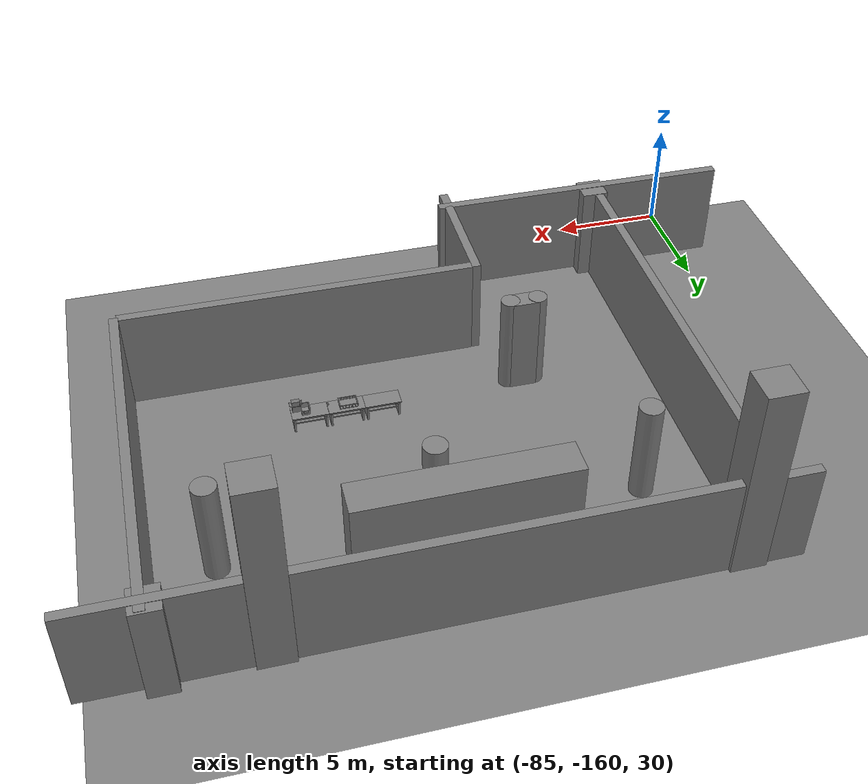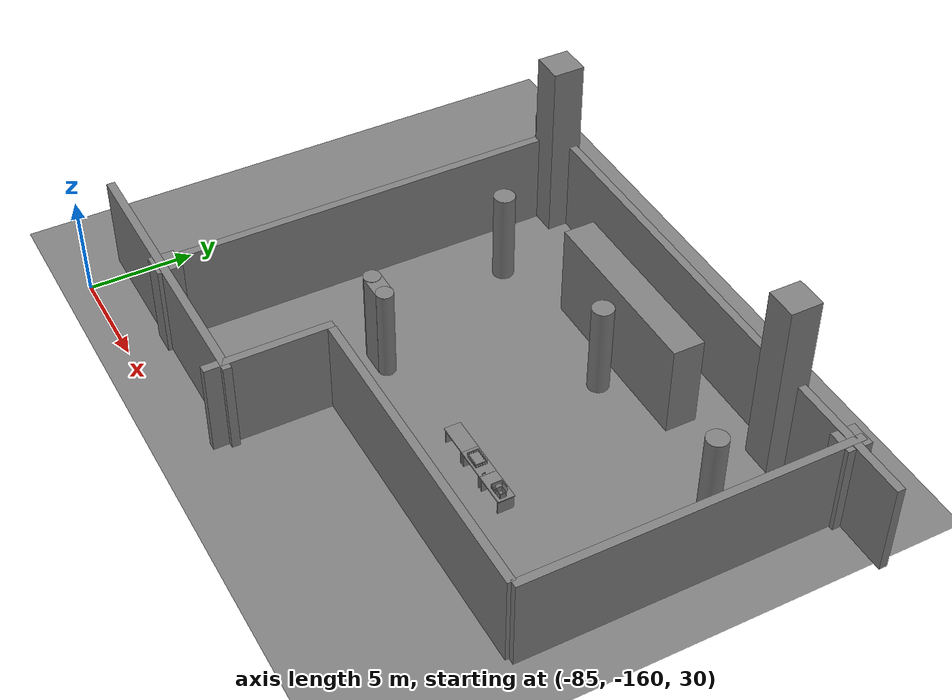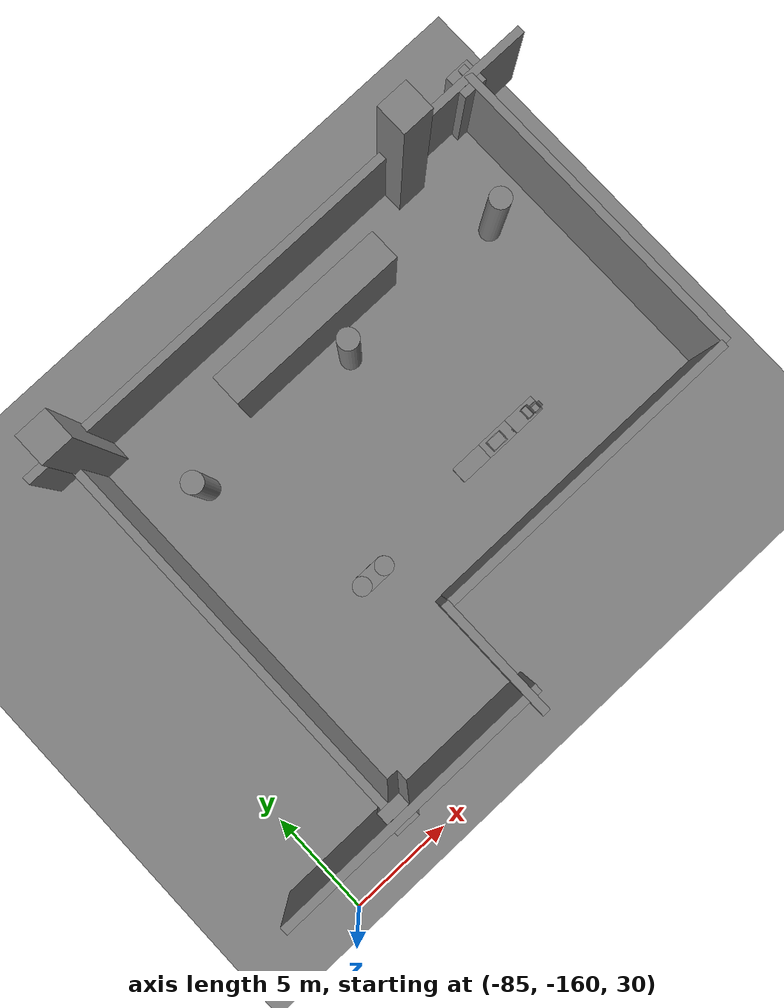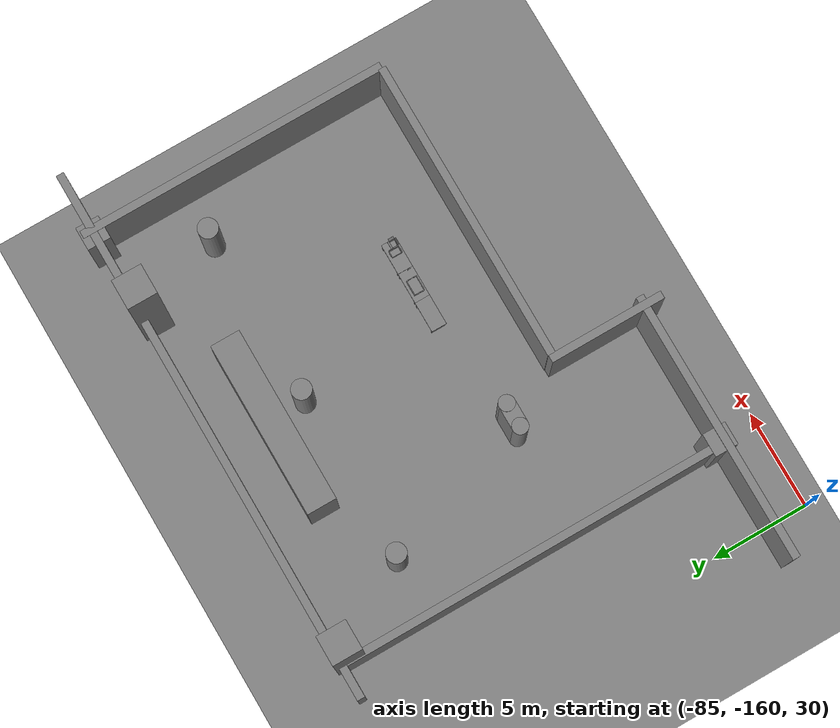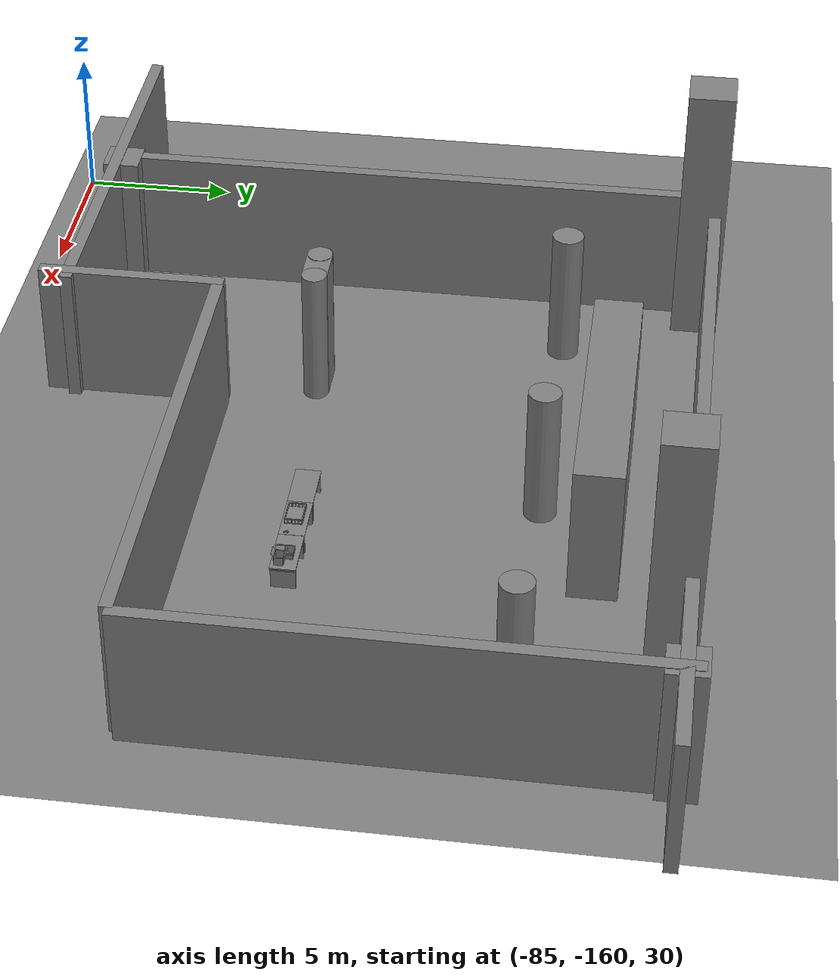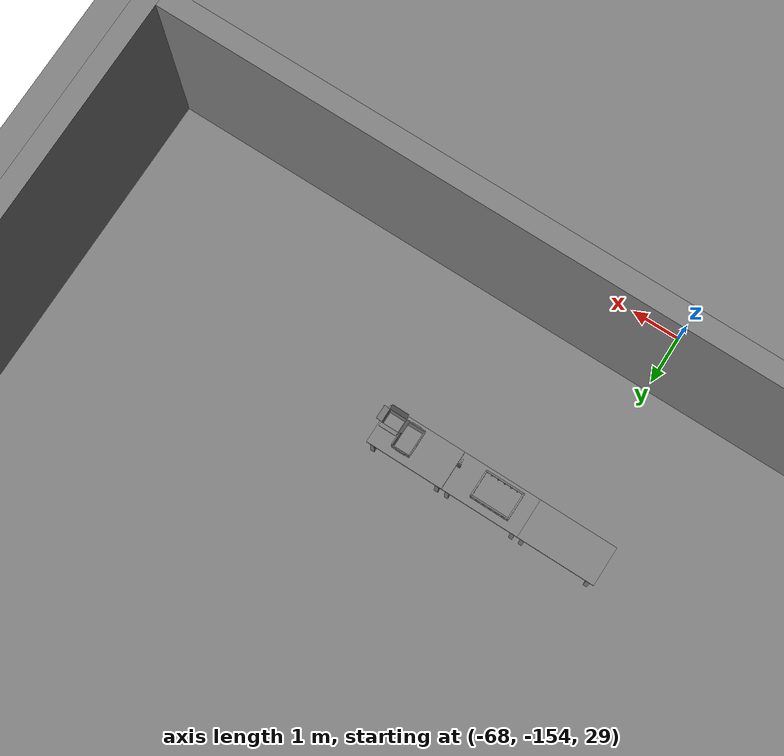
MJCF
<mujoco>
    <option gravity="0.000000000 0.000000000 -9.810000420" timestep="0.0049999999" integrator="implicitfast" density="1.225" viscosity="1.8000001e-05" noslip_iterations="10" iterations="100" sdf_iterations="50">
        <flag multiccd="disable"/>
    </option>
    <size memory="1000M"/>
    <compiler coordinate="local"/>
    <worldbody>
        <light cutoff="30" pos="0 1 1" dir="0 -1 -2"/>
        <light cutoff="30" pos="0 -1 1" dir="0 1 -2"/>
        <body pos="-64.866622925 -149.383972168 30.183746338" euler="89.999992371 89.999946594 0.000000000" name="openloong_gripper_2f85_fix_base_usda_bluebox_01">
            <geom contype="1" conaffinity="1" density="1000" type="box" material="" rgba="0.500000000 0.500000000 0.500000000 1.000000000" solimp="0.899999976 0.949999988 0.001000000" friction="1.000000000 0.005000000 0.000100000" solref="0.020000000 1.000000000" margin="0" condim="3" group="0" pos="0.276596069 0.187225342 0.000061035" quat="0.707107008 0.000077501 0.707106471 0.000077456" size="0.100000001 0.057999998 0.010000000" name="openloong_gripper_2f85_fix_base_usda_geom_B2244B8C_9295_4BD5_99C7_6E8CE6595DFB"/>
            <geom contype="1" conaffinity="1" density="1000" type="box" material="" rgba="0.500000000 0.500000000 0.500000000 1.000000000" solimp="0.899999976 0.949999988 0.001000000" friction="1.000000000 0.005000000 0.000100000" solref="0.020000000 1.000000000" margin="0" condim="3" group="0" pos="0.000000000 0.002883911 0.000000000" quat="1.000000000 0.000000000 0.000000000 0.000000000" size="0.254000008 0.003000000 0.172000006" name="openloong_gripper_2f85_fix_base_usda_geom_BBCEDAA6_D501_4147_8086_3991936EBB2A"/>
            <geom contype="1" conaffinity="1" density="1000" type="box" material="" rgba="0.500000000 0.500000000 0.500000000 1.000000000" solimp="0.899999976 0.949999988 0.001000000" friction="1.000000000 0.005000000 0.000100000" solref="0.020000000 1.000000000" margin="0" condim="3" group="0" pos="0.000015259 0.124874115 0.173477173" quat="0.999796450 0.020176515 -0.000000015 0.000000030" size="0.259999990 0.119999997 0.007000000" name="openloong_gripper_2f85_fix_base_usda_geom_F737F737_E1AA_4DC8_AFEC_71C5F7CE7021"/>
            <geom contype="1" conaffinity="1" density="1000" type="box" material="" rgba="0.500000000 0.500000000 0.500000000 1.000000000" solimp="0.899999976 0.949999988 0.001000000" friction="1.000000000 0.005000000 0.000100000" solref="0.020000000 1.000000000" margin="0" condim="3" group="0" pos="0.000015259 0.124874115 -0.173477173" quat="0.999796450 -0.020176545 -0.000000015 0.000000000" size="0.259999990 0.119999997 0.007000000" name="openloong_gripper_2f85_fix_base_usda_geom_E389751B_3A93_49C0_A5A7_AC4DF7B72730"/>
            <geom contype="1" conaffinity="1" density="1000" type="box" material="" rgba="0.500000000 0.500000000 0.500000000 1.000000000" solimp="0.899999976 0.949999988 0.001000000" friction="1.000000000 0.005000000 0.000100000" solref="0.020000000 1.000000000" margin="0" condim="3" group="0" pos="0.000015259 0.214012146 0.188980103" quat="0.999913096 0.013176724 0.000000015 0.000000000" size="0.259999990 0.029999999 0.012500000" name="openloong_gripper_2f85_fix_base_usda_geom_EC983757_CFCD_4190_A3F2_CDF6023DF4D7"/>
            <geom contype="1" conaffinity="1" density="1000" type="box" material="" rgba="0.500000000 0.500000000 0.500000000 1.000000000" solimp="0.899999976 0.949999988 0.001000000" friction="1.000000000 0.005000000 0.000100000" solref="0.020000000 1.000000000" margin="0" condim="3" group="0" pos="-0.258346558 0.125289917 0.001876831" quat="0.702796996 -0.020792052 0.710783184 0.020769238" size="0.189999998 0.119999997 0.009000000" name="openloong_gripper_2f85_fix_base_usda_geom_F6709B2C_B0FC_4331_906D_1120D7A7C6B4"/>
            <geom contype="1" conaffinity="1" density="1000" type="box" material="" rgba="0.500000000 0.500000000 0.500000000 1.000000000" solimp="0.899999976 0.949999988 0.001000000" friction="1.000000000 0.005000000 0.000100000" solref="0.020000000 1.000000000" margin="0" condim="3" group="0" pos="0.000015259 0.214012146 -0.188980103" quat="0.999913096 -0.013176769 0.000000030 0.000000015" size="0.259999990 0.029999999 0.012500000" name="openloong_gripper_2f85_fix_base_usda_geom_4FAACCB7_B7F9_4E78_8862_A4ECED9FF3FF"/>
            <geom contype="1" conaffinity="1" density="1000" type="box" material="" rgba="0.500000000 0.500000000 0.500000000 1.000000000" solimp="0.899999976 0.949999988 0.001000000" friction="1.000000000 0.005000000 0.000100000" solref="0.020000000 1.000000000" margin="0" condim="3" group="0" pos="-0.276596069 0.187225342 0.000061035" quat="0.707106650 0.000077441 0.707106709 0.000077456" size="0.100000001 0.057999998 0.010000000" name="openloong_gripper_2f85_fix_base_usda_geom_E5F20AD4_3432_4AF2_B0FF_B34AFD7BF1B4"/>
            <geom contype="1" conaffinity="1" density="1000" type="box" material="" rgba="0.500000000 0.500000000 0.500000000 1.000000000" solimp="0.899999976 0.949999988 0.001000000" friction="1.000000000 0.005000000 0.000100000" solref="0.020000000 1.000000000" margin="0" condim="3" group="0" pos="0.258346558 0.125289917 0.001876831" quat="0.702851534 0.018856451 0.710823834 -0.019329429" size="0.189999998 0.119999997 0.009000000" name="openloong_gripper_2f85_fix_base_usda_geom_92527F27_1ED2_4753_BCBD_C4659132FE22"/>
            <freejoint name="openloong_gripper_2f85_fix_base_usda_bluebox_01_joint"/>
            <site size="0.005000000 0.005000000 0.005000000" rgba="0.500000000 0.500000000 0.500000000 1.000000000" pos="0.000000000 0.000000000 0.000000000" quat="0.999961913 0.008726534 0.000000000 0.000000000" group="0" type="sphere" name="openloong_gripper_2f85_fix_base_usda_bluebox_01site"/>
        </body>
        <body pos="-64.496299744 -149.491867065 30.235729218" euler="0.000000000 0.000000000 89.999946594" name="openloong_gripper_2f85_fix_base_usda_cardboardbox_01">
            <geom contype="1" conaffinity="1" density="1000" type="box" material="" rgba="0.500000000 0.500000000 0.500000000 1.000000000" solimp="0.899999976 0.949999988 0.001000000" friction="1.000000000 0.005000000 0.000100000" solref="0.020000000 1.000000000" margin="0" condim="3" group="0" pos="-0.003166199 -0.004086494 0.005052090" quat="1.000000000 0.000000000 0.000000000 0.000000000" size="0.142499998 0.177500010 0.005000000" name="openloong_gripper_2f85_fix_base_usda_geom_20169C57_4ED6_4CE1_A8C1_B05B0AB52A75"/>
            <geom contype="1" conaffinity="1" density="1000" type="box" material="" rgba="0.500000000 0.500000000 0.500000000 1.000000000" solimp="0.899999976 0.949999988 0.001000000" friction="1.000000000 0.005000000 0.000100000" solref="0.020000000 1.000000000" margin="0" condim="3" group="0" pos="-0.003166199 0.170316696 0.150570869" quat="1.000000000 0.000000000 0.000000000 0.000000000" size="0.142499998 0.005000000 0.149999991" name="openloong_gripper_2f85_fix_base_usda_geom_5E6EDE71_FCC2_481D_B475_03D38E147BB3"/>
            <geom contype="1" conaffinity="1" density="1000" type="box" material="" rgba="0.500000000 0.500000000 0.500000000 1.000000000" solimp="0.899999976 0.949999988 0.001000000" friction="1.000000000 0.005000000 0.000100000" solref="0.020000000 1.000000000" margin="0" condim="3" group="0" pos="-0.147399902 -0.005307198 0.150570869" quat="1.000000000 0.000000000 0.000000000 0.000000000" size="0.005000000 0.177500010 0.149999991" name="openloong_gripper_2f85_fix_base_usda_geom_F2DE1B20_400C_4BA7_9D59_50FAC5A8D102"/>
            <geom contype="1" conaffinity="1" density="1000" type="box" material="" rgba="0.500000000 0.500000000 0.500000000 1.000000000" solimp="0.899999976 0.949999988 0.001000000" friction="1.000000000 0.005000000 0.000100000" solref="0.020000000 1.000000000" margin="0" condim="3" group="0" pos="0.140275955 -0.005307198 0.150570869" quat="1.000000000 0.000000000 0.000000000 0.000000000" size="0.005000000 0.177500010 0.149999991" name="openloong_gripper_2f85_fix_base_usda_geom_05BDF970_4385_46EA_BA2A_B77A41F738FC"/>
            <geom contype="1" conaffinity="1" density="1000" type="box" material="" rgba="0.500000000 0.500000000 0.500000000 1.000000000" solimp="0.899999976 0.949999988 0.001000000" friction="1.000000000 0.005000000 0.000100000" solref="0.020000000 1.000000000" margin="0" condim="3" group="0" pos="-0.003166199 -0.181550980 0.150570869" quat="1.000000000 0.000000000 0.000000000 0.000000000" size="0.142499998 0.005000000 0.149999991" name="openloong_gripper_2f85_fix_base_usda_geom_BB89CA20_469D_4A66_BC48_79CCAF3794A2"/>
            <freejoint name="openloong_gripper_2f85_fix_base_usda_cardboardbox_01_joint"/>
            <site size="0.005000000 0.005000000 0.005000000" rgba="0.500000000 0.500000000 0.500000000 1.000000000" pos="0.000000000 0.000000000 0.000000000" quat="0.999961913 0.008726535 0.000000000 0.000000000" group="0" type="sphere" name="openloong_gripper_2f85_fix_base_usda_site_87465FDA_C5D6_46D1_829F_F0AAF11A9020"/>
            <body pos="0.139160156 -0.004048347 0.301930904" euler="-179.999954224 49.383502960 179.999954224" name="openloong_gripper_2f85_fix_base_usda_A1_006">
                <geom contype="1" conaffinity="1" density="1000" type="box" material="" rgba="0.500000000 0.500000000 0.500000000 1.000000000" solimp="0.899999976 0.949999988 0.001000000" friction="1.000000000 0.005000000 0.000100000" solref="0.020000000 1.000000000" margin="0" condim="3" group="0" pos="-0.071587563 0.000009537 0.001745224" quat="0.999999881 0.000000000 0.000000000 0.000000000" size="0.071249999 0.179999992 0.002500000" name="openloong_gripper_2f85_fix_base_usda_geom_099D202B_4C16_486B_9447_4AF9279B6539"/>
                <joint armature="0" stiffness="0.07" damping="0.0099999998" axis="0.000000 1.000000 0.000000" type="hinge" name="openloong_gripper_2f85_fix_base_usda_A1_006"/>
            </body>
            <body pos="-0.145902634 -0.004086494 0.301938057" euler="-180.000000000 -60.000011444 -180.000000000" name="openloong_gripper_2f85_fix_base_usda_A2_006">
                <geom contype="1" conaffinity="1" density="1000" type="box" material="" rgba="0.500000000 0.500000000 0.500000000 1.000000000" solimp="0.899999976 0.949999988 0.001000000" friction="1.000000000 0.005000000 0.000100000" solref="0.020000000 1.000000000" margin="0" condim="3" group="0" pos="0.071268082 0.000009537 0.002717972" quat="0.000002921 0.000000000 -0.000000030 0.999999881" size="0.071249999 0.179999992 0.002500000" name="openloong_gripper_2f85_fix_base_usda_geom_3D559A3E_B01E_4D16_A982_4163E6584D3A"/>
                <joint armature="0" stiffness="0.07" damping="0.0099999998" axis="0.000000 1.000000 0.000000" type="hinge" name="openloong_gripper_2f85_fix_base_usda_A2_006"/>
            </body>
            <body pos="-0.003385544 0.175991058 0.301930904" euler="-125.858116150 -0.000004561 0.000002331" name="openloong_gripper_2f85_fix_base_usda_B2_006">
                <geom contype="1" conaffinity="1" density="1000" type="box" material="" rgba="0.500000000 0.500000000 0.500000000 1.000000000" solimp="0.899999976 0.949999988 0.001000000" friction="1.000000000 0.005000000 0.000100000" solref="0.020000000 1.000000000" margin="0" condim="3" group="0" pos="0.000009537 -0.070939064 -0.002470016" quat="0.999614120 0.027776197 -0.000000015 0.000000030" size="0.137500003 0.064999998 0.005000000" name="openloong_gripper_2f85_fix_base_usda_geom_0D102E6F_3042_4AE7_A3F8_21295F62F5BD"/>
                <joint armature="0" stiffness="0.07" damping="0.0099999998" axis="1.000000 0.000000 0.000000" type="hinge" name="openloong_gripper_2f85_fix_base_usda_B2_006"/>
            </body>
            <body pos="-0.003385544 -0.184140205 0.301938057" euler="147.805557251 0.000000000 0.000000000" name="openloong_gripper_2f85_fix_base_usda_B1_006">
                <geom contype="1" conaffinity="1" density="1000" type="box" material="" rgba="0.500000000 0.500000000 0.500000000 1.000000000" solimp="0.899999976 0.949999988 0.001000000" friction="1.000000000 0.005000000 0.000100000" solref="0.020000000 1.000000000" margin="0" condim="3" group="0" pos="-0.000028610 0.070202351 -0.002703667" quat="0.999614179 -0.027776167 0.000000000 0.000000000" size="0.137500003 0.064999998 0.005000000" name="openloong_gripper_2f85_fix_base_usda_geom_422A07C9_A603_4556_8CBB_18DC8C99A957"/>
                <joint armature="0" stiffness="0.07" damping="0.0099999998" axis="1.000000 0.000000 0.000000" type="hinge" name="openloong_gripper_2f85_fix_base_usda_B1_006"/>
            </body>
        </body>
        <body pos="-65.882858276 -149.481979370 30.229999542" euler="-64.487716675 0.000000000 0.000000000" name="openloong_gripper_2f85_fix_base_usda_Barcode">
            <geom contype="1" conaffinity="1" density="1000" type="box" material="" rgba="0.500000000 0.500000000 0.500000000 1.000000000" solimp="0.899999976 0.949999988 0.001000000" friction="1.000000000 0.005000000 0.000100000" solref="0.020000000 1.000000000" margin="0" condim="3" group="0" pos="0.000000000 0.013038635 0.001419067" quat="0.000000000 0.000000000 0.000000000 1.000000119" size="0.034000002 0.010000000 0.017999999" name="openloong_gripper_2f85_fix_base_usda_geom_B1C29D1B_AAC1_4C49_8D53_6493D0A68CFA"/>
            <geom contype="1" conaffinity="1" density="1000" type="box" material="" rgba="0.500000000 0.500000000 0.500000000 1.000000000" solimp="0.899999976 0.949999988 0.001000000" friction="1.000000000 0.005000000 0.000100000" solref="0.020000000 1.000000000" margin="0" condim="3" group="0" pos="0.000000000 -0.035301208 -0.007095337" quat="0.000000000 0.000000000 -0.043619365 0.999048233" size="0.028999999 0.010000000 0.020000000" name="openloong_gripper_2f85_fix_base_usda_geom_06BFE5F0_DC19_4351_8433_F5F4A808F1C7"/>
            <geom contype="1" conaffinity="1" density="1000" type="box" material="" rgba="0.500000000 0.500000000 0.500000000 1.000000000" solimp="0.899999976 0.949999988 0.001000000" friction="1.000000000 0.005000000 0.000100000" solref="0.020000000 1.000000000" margin="0" condim="3" group="0" pos="0.000000000 -0.043411255 -0.011749268" quat="0.922262907 0.386563420 0.000000000 0.000000000" size="0.026000001 0.010000000 0.020000000" name="openloong_gripper_2f85_fix_base_usda_geom_7B997A00_5BF2_458E_BD36_A3DC76488A35"/>
            <geom contype="1" conaffinity="1" density="1000" type="box" material="" rgba="0.500000000 0.500000000 0.500000000 1.000000000" solimp="0.899999976 0.949999988 0.001000000" friction="1.000000000 0.005000000 0.000100000" solref="0.020000000 1.000000000" margin="0" condim="3" group="0" pos="0.000000000 -0.016967773 -0.031860352" quat="0.000000000 0.000000000 0.000000000 1.000000119" size="0.008000000 0.010000000 0.013000000" name="openloong_gripper_2f85_fix_base_usda_geom_BC33776E_DF49_4775_8C83_2411B4A1FB67"/>
            <geom contype="1" conaffinity="1" density="1000" type="box" material="" rgba="0.500000000 0.500000000 0.500000000 1.000000000" solimp="0.899999976 0.949999988 0.001000000" friction="1.000000000 0.005000000 0.000100000" solref="0.020000000 1.000000000" margin="0" condim="3" group="0" pos="0.000000000 -0.001869202 0.000312805" quat="0.953716993 0.300705761 0.000000000 0.000000000" size="0.032000002 0.010000000 0.018999999" name="openloong_gripper_2f85_fix_base_usda_geom_39784899_7682_4572_B185_FD4B3FD5E70A"/>
            <geom contype="1" conaffinity="1" density="1000" type="box" material="" rgba="0.500000000 0.500000000 0.500000000 1.000000000" solimp="0.899999976 0.949999988 0.001000000" friction="1.000000000 0.005000000 0.000100000" solref="0.020000000 1.000000000" margin="0" condim="3" group="0" pos="0.000000000 -0.019531250 -0.003173828" quat="0.953716993 0.300705761 0.000000000 0.000000000" size="0.030999999 0.010000000 0.020000000" name="openloong_gripper_2f85_fix_base_usda_geom_B47527C6_C4B1_4D54_9E3B_A0C59D315B42"/>
            <geom contype="1" conaffinity="1" density="1000" type="box" material="" rgba="0.500000000 0.500000000 0.500000000 1.000000000" solimp="0.899999976 0.949999988 0.001000000" friction="1.000000000 0.005000000 0.000100000" solref="0.020000000 1.000000000" margin="0" condim="3" group="0" pos="0.000000000 -0.035301208 -0.007095337" quat="0.953716993 0.300705761 0.000000000 0.000000000" size="0.028999999 0.010000000 0.020000000" name="openloong_gripper_2f85_fix_base_usda_geom_8E461227_409A_412D_87B8_044F0AF59978"/>
            <geom contype="1" conaffinity="1" density="1000" type="box" material="" rgba="0.500000000 0.500000000 0.500000000 1.000000000" solimp="0.899999976 0.949999988 0.001000000" friction="1.000000000 0.005000000 0.000100000" solref="0.020000000 1.000000000" margin="0" condim="3" group="0" pos="0.000000000 -0.042617798 -0.071121216" quat="0.000000000 0.000000000 0.000000000 1.000000119" size="0.013000000 0.021000000 0.059999999" name="openloong_gripper_2f85_fix_base_usda_geom_8D17DA23_F572_4035_A488_94B89502DAE3"/>
            <freejoint name="openloong_gripper_2f85_fix_base_usda_Barcode_joint"/>
            <site size="0.005000000 0.005000000 0.005000000" rgba="0.500000000 0.500000000 0.500000000 1.000000000" pos="0.000000000 0.000000000 0.000000000" quat="1.000000000 0.000000000 0.000000000 0.000000000" group="0" type="sphere" name="openloong_gripper_2f85_fix_base_usda_Barcode_site"/>
        </body>
        <body pos="-66.745018005 -149.392349243 30.184000015" euler="0.000000000 0.000000000 89.999946594" name="[22331980948769]_Basket_01">
            <geom contype="1" conaffinity="1" density="1000" type="box" material="" rgba="0.500000000 0.500000000 0.500000000 1.000000000" solimp="0.899999976 0.949999988 0.001000000" friction="1.000000000 0.005000000 0.000100000" solref="0.020000000 1.000000000" margin="0" condim="3" group="0" pos="-0.052425385 0.389207840 0.089787483" quat="0.707107008 0.000000000 0.000000000 0.707106411" size="0.014249999 0.014249999 0.059999999" name="[22331980948769]_geom_F896CCAA_2F96_4250_8AEC_5BD4B76D669D"/>
            <geom contype="1" conaffinity="1" density="1000" type="box" material="" rgba="0.500000000 0.500000000 0.500000000 1.000000000" solimp="0.899999976 0.949999988 0.001000000" friction="1.000000000 0.005000000 0.000100000" solref="0.020000000 1.000000000" margin="0" condim="3" group="0" pos="0.264015198 -0.133043289 0.089787483" quat="0.707107008 0.000000000 0.000000000 0.707106411" size="0.014249999 0.014249999 0.059999999" name="[22331980948769]_geom_D1CD8B8F_B1ED_497B_B591_1671B5875537"/>
            <geom contype="1" conaffinity="1" density="1000" type="box" material="" rgba="0.500000000 0.500000000 0.500000000 1.000000000" solimp="0.899999976 0.949999988 0.001000000" friction="1.000000000 0.005000000 0.000100000" solref="0.020000000 1.000000000" margin="0" condim="3" group="0" pos="-0.264015198 -0.265548706 0.089793205" quat="0.707107008 0.000000000 0.000000000 0.707106411" size="0.014249999 0.014249999 0.059999999" name="[22331980948769]_geom_64D93496_A7E8_4E55_A94A_99960D1177B0"/>
            <geom contype="1" conaffinity="1" density="1000" type="box" material="" rgba="0.500000000 0.500000000 0.500000000 1.000000000" solimp="0.899999976 0.949999988 0.001000000" friction="1.000000000 0.005000000 0.000100000" solref="0.020000000 1.000000000" margin="0" condim="3" group="0" pos="-0.160263062 -0.389322281 0.089793205" quat="0.707107008 0.000000000 0.000000000 0.707106411" size="0.014249999 0.014249999 0.059999999" name="[22331980948769]_geom_515CE060_4A08_4C20_A975_02D317C7CFA6"/>
            <geom contype="1" conaffinity="1" density="1000" type="box" material="" rgba="0.500000000 0.500000000 0.500000000 1.000000000" solimp="0.899999976 0.949999988 0.001000000" friction="1.000000000 0.005000000 0.000100000" solref="0.020000000 1.000000000" margin="0" condim="3" group="0" pos="0.162265778 -0.389322281 0.089787483" quat="0.707107008 0.000000000 0.000000000 0.707106411" size="0.014249999 0.014249999 0.059999999" name="[22331980948769]_geom_DF8728C7_6C2D_49E8_AA13_D8DB030468EF"/>
            <geom contype="1" conaffinity="1" density="1000" type="box" material="" rgba="0.500000000 0.500000000 0.500000000 1.000000000" solimp="0.899999976 0.949999988 0.001000000" friction="1.000000000 0.005000000 0.000100000" solref="0.020000000 1.000000000" margin="0" condim="3" group="0" pos="0.264015198 0.389207840 0.089787483" quat="0.707107008 0.000000000 0.000000000 0.707106411" size="0.014249999 0.014249999 0.059999999" name="[22331980948769]_geom_923B4589_B9AB_45D9_9E66_273317D9CCA3"/>
            <geom contype="1" conaffinity="1" density="1000" type="box" material="" rgba="0.500000000 0.500000000 0.500000000 1.000000000" solimp="0.899999976 0.949999988 0.001000000" friction="1.000000000 0.005000000 0.000100000" solref="0.020000000 1.000000000" margin="0" condim="3" group="0" pos="-0.264015198 -0.133043289 0.089793205" quat="0.707107008 0.000000000 0.000000000 0.707106411" size="0.014249999 0.014249999 0.059999999" name="[22331980948769]_geom_18965573_5D4A_4861_ACBD_9ACC49B5DB6B"/>
            <geom contype="1" conaffinity="1" density="1000" type="box" material="" rgba="0.500000000 0.500000000 0.500000000 1.000000000" solimp="0.899999976 0.949999988 0.001000000" friction="1.000000000 0.005000000 0.000100000" solref="0.020000000 1.000000000" margin="0" condim="3" group="0" pos="-0.264026642 0.269256592 0.089793205" quat="0.707107008 0.000000000 0.000000000 0.707106411" size="0.014249999 0.014249999 0.059999999" name="[22331980948769]_geom_A221E8D1_031D_4A7F_8E0B_04DDA0B71024"/>
            <geom contype="1" conaffinity="1" density="1000" type="box" material="" rgba="0.500000000 0.500000000 0.500000000 1.000000000" solimp="0.899999976 0.949999988 0.001000000" friction="1.000000000 0.005000000 0.000100000" solref="0.020000000 1.000000000" margin="0" condim="3" group="0" pos="0.054462433 0.389207840 0.089787483" quat="0.707107008 0.000000000 0.000000000 0.707106411" size="0.014249999 0.014249999 0.059999999" name="[22331980948769]_geom_DF28A277_7652_4085_B0E7_05F8884AE31C"/>
            <geom contype="1" conaffinity="1" density="1000" type="box" material="" rgba="0.500000000 0.500000000 0.500000000 1.000000000" solimp="0.899999976 0.949999988 0.001000000" friction="1.000000000 0.005000000 0.000100000" solref="0.020000000 1.000000000" margin="0" condim="3" group="0" pos="0.054462433 -0.389322281 0.089787483" quat="0.707107008 0.000000000 0.000000000 0.707106411" size="0.014249999 0.014249999 0.059999999" name="[22331980948769]_geom_9CC0DE3A_8E1D_4BEC_885D_FEC9D5E0F4BB"/>
            <geom contype="1" conaffinity="1" density="1000" type="box" material="" rgba="0.500000000 0.500000000 0.500000000 1.000000000" solimp="0.899999976 0.949999988 0.001000000" friction="1.000000000 0.005000000 0.000100000" solref="0.020000000 1.000000000" margin="0" condim="3" group="0" pos="0.264015198 0.269256592 0.089793205" quat="0.707107008 0.000000000 0.000000000 0.707106411" size="0.014249999 0.014249999 0.059999999" name="[22331980948769]_geom_AB5C5CA2_3E3E_4E72_B235_4CF3D6568E3E"/>
            <geom contype="1" conaffinity="1" density="1000" type="box" material="" rgba="0.500000000 0.500000000 0.500000000 1.000000000" solimp="0.899999976 0.949999988 0.001000000" friction="1.000000000 0.005000000 0.000100000" solref="0.020000000 1.000000000" margin="0" condim="3" group="0" pos="0.264015198 -0.389322281 0.089787483" quat="0.707107008 0.000000000 0.000000000 0.707106411" size="0.014249999 0.014249999 0.059999999" name="[22331980948769]_geom_9B8EA465_2395_4647_B63F_5A27E6AD6218"/>
            <geom contype="1" conaffinity="1" density="1000" type="box" material="" rgba="0.500000000 0.500000000 0.500000000 1.000000000" solimp="0.899999976 0.949999988 0.001000000" friction="1.000000000 0.005000000 0.000100000" solref="0.020000000 1.000000000" margin="0" condim="3" group="0" pos="0.000000000 0.000000000 0.015998840" quat="0.707107008 0.000000000 0.000000000 0.707106411" size="0.403499991 0.279000014 0.015750000" name="[22331980948769]_geom_E576029B_270F_410E_B4C6_D1D0E41551BB"/>
            <geom contype="1" conaffinity="1" density="1000" type="box" material="" rgba="0.500000000 0.500000000 0.500000000 1.000000000" solimp="0.899999976 0.949999988 0.001000000" friction="1.000000000 0.005000000 0.000100000" solref="0.020000000 1.000000000" margin="0" condim="3" group="0" pos="0.000000000 -0.389476776 0.163619041" quat="0.707107008 0.000000000 0.000000000 0.707106411" size="0.015000000 0.277500004 0.015750000" name="[22331980948769]_geom_B7A2C17B_C518_4088_A55C_7AB04BFC2B7D"/>
            <geom contype="1" conaffinity="1" density="1000" type="box" material="" rgba="0.500000000 0.500000000 0.500000000 1.000000000" solimp="0.899999976 0.949999988 0.001000000" friction="1.000000000 0.005000000 0.000100000" solref="0.020000000 1.000000000" margin="0" condim="3" group="0" pos="0.162265778 0.389207840 0.089787483" quat="0.707107008 0.000000000 0.000000000 0.707106411" size="0.014249999 0.014249999 0.059999999" name="[22331980948769]_geom_BD2C5620_4403_439C_8E8B_A953DD807FE5"/>
            <geom contype="1" conaffinity="1" density="1000" type="box" material="" rgba="0.500000000 0.500000000 0.500000000 1.000000000" solimp="0.899999976 0.949999988 0.001000000" friction="1.000000000 0.005000000 0.000100000" solref="0.020000000 1.000000000" margin="0" condim="3" group="0" pos="0.000000000 0.389471054 0.163619041" quat="0.707107008 0.000000000 0.000000000 0.707106411" size="0.015000000 0.277500004 0.015750000" name="[22331980948769]_geom_F1B05A78_A5E6_447C_A61C_BA9844977A9F"/>
            <geom contype="1" conaffinity="1" density="1000" type="box" material="" rgba="0.500000000 0.500000000 0.500000000 1.000000000" solimp="0.899999976 0.949999988 0.001000000" friction="1.000000000 0.005000000 0.000100000" solref="0.020000000 1.000000000" margin="0" condim="3" group="0" pos="-0.263511658 0.000000000 0.163619041" quat="0.707107008 0.000000000 0.000000000 0.707106411" size="0.403499991 0.015000000 0.015750000" name="[22331980948769]_geom_792013BA_D2FA_4F47_94A3_2FE85F35F0BB"/>
            <geom contype="1" conaffinity="1" density="1000" type="box" material="" rgba="0.500000000 0.500000000 0.500000000 1.000000000" solimp="0.899999976 0.949999988 0.001000000" friction="1.000000000 0.005000000 0.000100000" solref="0.020000000 1.000000000" margin="0" condim="3" group="0" pos="-0.264015198 0.141334534 0.089793205" quat="0.707107008 0.000000000 0.000000000 0.707106411" size="0.014249999 0.014249999 0.059999999" name="[22331980948769]_geom_17318788_B97E_4B55_AFA4_92D872E9E232"/>
            <geom contype="1" conaffinity="1" density="1000" type="box" material="" rgba="0.500000000 0.500000000 0.500000000 1.000000000" solimp="0.899999976 0.949999988 0.001000000" friction="1.000000000 0.005000000 0.000100000" solref="0.020000000 1.000000000" margin="0" condim="3" group="0" pos="0.264015198 -0.265548706 0.089787483" quat="0.707107008 0.000000000 0.000000000 0.707106411" size="0.014249999 0.014249999 0.059999999" name="[22331980948769]_geom_0EC97C6D_6F4B_4937_8E9A_4585350970B8"/>
            <geom contype="1" conaffinity="1" density="1000" type="box" material="" rgba="0.500000000 0.500000000 0.500000000 1.000000000" solimp="0.899999976 0.949999988 0.001000000" friction="1.000000000 0.005000000 0.000100000" solref="0.020000000 1.000000000" margin="0" condim="3" group="0" pos="-0.160263062 0.389207840 0.089787483" quat="0.707107008 0.000000000 0.000000000 0.707106411" size="0.014249999 0.014249999 0.059999999" name="[22331980948769]_geom_31BEAA1D_66EC_4D26_A8E7_D2CF0E9CFF84"/>
            <geom contype="1" conaffinity="1" density="1000" type="box" material="" rgba="0.500000000 0.500000000 0.500000000 1.000000000" solimp="0.899999976 0.949999988 0.001000000" friction="1.000000000 0.005000000 0.000100000" solref="0.020000000 1.000000000" margin="0" condim="3" group="0" pos="-0.052425385 -0.389322281 0.089787483" quat="0.707107008 0.000000000 0.000000000 0.707106411" size="0.014249999 0.014249999 0.059999999" name="[22331980948769]_geom_C0777E00_411F_49B3_BFCA_4F13AF4C5781"/>
            <geom contype="1" conaffinity="1" density="1000" type="box" material="" rgba="0.500000000 0.500000000 0.500000000 1.000000000" solimp="0.899999976 0.949999988 0.001000000" friction="1.000000000 0.005000000 0.000100000" solref="0.020000000 1.000000000" margin="0" condim="3" group="0" pos="-0.264026642 -0.389322281 0.089793205" quat="0.707107008 0.000000000 0.000000000 0.707106411" size="0.014249999 0.014249999 0.059999999" name="[22331980948769]_geom_C7D5EC70_B72F_4303_A2B6_CD4F7298B247"/>
            <geom contype="1" conaffinity="1" density="1000" type="box" material="" rgba="0.500000000 0.500000000 0.500000000 1.000000000" solimp="0.899999976 0.949999988 0.001000000" friction="1.000000000 0.005000000 0.000100000" solref="0.020000000 1.000000000" margin="0" condim="3" group="0" pos="0.264015198 0.141334534 0.089787483" quat="0.707107008 0.000000000 0.000000000 0.707106411" size="0.014249999 0.014249999 0.059999999" name="[22331980948769]_geom_3B6F1D10_5090_474D_BA52_8AE0D543EB38"/>
            <geom contype="1" conaffinity="1" density="1000" type="box" material="" rgba="0.500000000 0.500000000 0.500000000 1.000000000" solimp="0.899999976 0.949999988 0.001000000" friction="1.000000000 0.005000000 0.000100000" solref="0.020000000 1.000000000" margin="0" condim="3" group="0" pos="-0.264015198 0.389207840 0.089793205" quat="0.707107008 0.000000000 0.000000000 0.707106411" size="0.014249999 0.014249999 0.059999999" name="[22331980948769]_geom_278C6F88_5880_4B9F_B799_498D28F016BA"/>
            <geom contype="1" conaffinity="1" density="1000" type="box" material="" rgba="0.500000000 0.500000000 0.500000000 1.000000000" solimp="0.899999976 0.949999988 0.001000000" friction="1.000000000 0.005000000 0.000100000" solref="0.020000000 1.000000000" margin="0" condim="3" group="0" pos="0.264015198 0.004480362 0.089787483" quat="0.707107008 0.000000000 0.000000000 0.707106411" size="0.014249999 0.014249999 0.059999999" name="[22331980948769]_geom_AF57827C_8B29_4C43_963A_211B5E64C42E"/>
            <geom contype="1" conaffinity="1" density="1000" type="box" material="" rgba="0.500000000 0.500000000 0.500000000 1.000000000" solimp="0.899999976 0.949999988 0.001000000" friction="1.000000000 0.005000000 0.000100000" solref="0.020000000 1.000000000" margin="0" condim="3" group="0" pos="0.263694763 -0.000011444 0.163619041" quat="0.707107008 0.000000000 0.000000000 0.707106411" size="0.403499991 0.015000000 0.015750000" name="[22331980948769]_geom_41AC29B2_51AB_4397_8C02_FD988B1B420A"/>
            <geom contype="1" conaffinity="1" density="1000" type="box" material="" rgba="0.500000000 0.500000000 0.500000000 1.000000000" solimp="0.899999976 0.949999988 0.001000000" friction="1.000000000 0.005000000 0.000100000" solref="0.020000000 1.000000000" margin="0" condim="3" group="0" pos="-0.264015198 0.004480362 0.089793205" quat="0.707107008 0.000000000 0.000000000 0.707106411" size="0.014249999 0.014249999 0.059999999" name="[22331980948769]_geom_950A122C_A145_4689_9BBA_E3F5F7A287B0"/>
            <freejoint name="[22331980948769]_joint_DA29376F_2ACC_4E66_8353_E1E09EDD0FCF"/>
        </body>
        <body pos="0.000000000 0.000000000 0.000000000" euler="0.000000000 0.000000000 0.000000000" name="Static Objects_Static Objects">
            <geom contype="1" conaffinity="1" density="1000" type="box" material="" rgba="0.500000000 0.500000000 0.500000000 1.000000000" solimp="0.899999976 0.949999988 0.001000000" friction="1.000000000 0.005000000 0.000100000" solref="0.020000000 1.000000000" margin="0" condim="3" group="0" pos="-67.544113159 -149.365814209 29.727830887" quat="0.500000417 0.499999970 0.499999553 0.499999970" size="0.381000012 0.319999993 0.041000001" name="Static Objects_geom_5787CF7A_C856_4676_891D_148A1683EF38"/>
            <geom contype="1" conaffinity="1" density="1000" type="box" material="" rgba="0.500000000 0.500000000 0.500000000 1.000000000" solimp="0.899999976 0.949999988 0.001000000" friction="1.000000000 0.005000000 0.000100000" solref="0.020000000 1.000000000" margin="0" condim="3" group="0" pos="-68.239501953 -149.365814209 30.086868286" quat="0.500000417 0.499999970 0.499999553 0.499999970" size="0.370999992 0.039500002 0.745000005" name="Static Objects_geom_686AE337_157F_4BA4_B3AE_92478E3F3BBC"/>
            <geom contype="1" conaffinity="1" density="1000" type="box" material="" rgba="0.500000000 0.500000000 0.500000000 1.000000000" solimp="0.899999976 0.949999988 0.001000000" friction="1.000000000 0.005000000 0.000100000" solref="0.020000000 1.000000000" margin="0" condim="3" group="0" pos="-68.239501953 -149.365814209 30.147235870" quat="0.500000417 0.499999970 0.499999553 0.499999970" size="0.400000006 0.022000000 0.800000012" name="Static Objects_geom_E5810C63_FBFD_4454_A7D4_7D9AF89DE278"/>
            <geom contype="1" conaffinity="1" density="1000" type="box" material="" rgba="0.500000000 0.500000000 0.500000000 1.000000000" solimp="0.899999976 0.949999988 0.001000000" friction="1.000000000 0.005000000 0.000100000" solref="0.020000000 1.000000000" margin="0" condim="3" group="0" pos="-68.934890747 -149.365814209 29.727830887" quat="0.500000417 0.499999970 0.499999553 0.499999970" size="0.381000012 0.319999993 0.041000001" name="Static Objects_geom_9446B3CD_2CCF_43C9_839B_C47B4398D7CA"/>
            <geom contype="1" conaffinity="1" density="1000" type="box" material="" rgba="0.500000000 0.500000000 0.500000000 1.000000000" solimp="0.899999976 0.949999988 0.001000000" friction="1.000000000 0.005000000 0.000100000" solref="0.020000000 1.000000000" margin="0" condim="3" group="0" pos="-68.239501953 -149.365814209 29.561563492" quat="0.500000417 0.499999970 0.499999553 0.499999970" size="0.020000000 0.022000000 0.660000026" name="Static Objects_geom_08559641_6BA8_4E32_AA76_D1BD336BD6C1"/>
            <geom contype="1" conaffinity="1" density="1000" type="box" material="" rgba="0.500000000 0.500000000 0.500000000 1.000000000" solimp="0.899999976 0.949999988 0.001000000" friction="1.000000000 0.005000000 0.000100000" solref="0.020000000 1.000000000" margin="0" condim="3" group="0" pos="-65.945671082 -149.365814209 29.727830887" quat="0.500000417 0.499999970 0.499999553 0.499999970" size="0.381000012 0.319999993 0.041000001" name="Static Objects_geom_023A7772_43C8_44C9_A27B_25D20DBB0DDE"/>
            <geom contype="1" conaffinity="1" density="1000" type="box" material="" rgba="0.500000000 0.500000000 0.500000000 1.000000000" solimp="0.899999976 0.949999988 0.001000000" friction="1.000000000 0.005000000 0.000100000" solref="0.020000000 1.000000000" margin="0" condim="3" group="0" pos="-66.641059875 -149.365814209 30.086868286" quat="0.500000417 0.499999970 0.499999553 0.499999970" size="0.370999992 0.039500002 0.745000005" name="Static Objects_geom_54454127_D5A1_4D46_8FDB_24312040B48F"/>
            <geom contype="1" conaffinity="1" density="1000" type="box" material="" rgba="0.500000000 0.500000000 0.500000000 1.000000000" solimp="0.899999976 0.949999988 0.001000000" friction="1.000000000 0.005000000 0.000100000" solref="0.020000000 1.000000000" margin="0" condim="3" group="0" pos="-66.641059875 -149.365814209 30.147235870" quat="0.500000417 0.499999970 0.499999553 0.499999970" size="0.400000006 0.022000000 0.800000012" name="Static Objects_geom_AFADBD33_5BD7_46CE_9D54_0BC75F2F7ABA"/>
            <geom contype="1" conaffinity="1" density="1000" type="box" material="" rgba="0.500000000 0.500000000 0.500000000 1.000000000" solimp="0.899999976 0.949999988 0.001000000" friction="1.000000000 0.005000000 0.000100000" solref="0.020000000 1.000000000" margin="0" condim="3" group="0" pos="-67.336448669 -149.365814209 29.727830887" quat="0.500000417 0.499999970 0.499999553 0.499999970" size="0.381000012 0.319999993 0.041000001" name="Static Objects_geom_824FEB3E_7CB0_4F3A_9E18_2417C2864C3D"/>
            <geom contype="1" conaffinity="1" density="1000" type="box" material="" rgba="0.500000000 0.500000000 0.500000000 1.000000000" solimp="0.899999976 0.949999988 0.001000000" friction="1.000000000 0.005000000 0.000100000" solref="0.020000000 1.000000000" margin="0" condim="3" group="0" pos="-66.641059875 -149.365814209 29.561563492" quat="0.500000417 0.499999970 0.499999553 0.499999970" size="0.020000000 0.022000000 0.660000026" name="Static Objects_geom_E31DBDE6_14A0_4528_8218_A9D935372154"/>
            <geom contype="1" conaffinity="1" density="1000" type="box" material="" rgba="0.500000000 0.500000000 0.500000000 1.000000000" solimp="0.899999976 0.949999988 0.001000000" friction="1.000000000 0.005000000 0.000100000" solref="0.020000000 1.000000000" margin="0" condim="3" group="0" pos="-64.338577271 -149.365814209 29.727830887" quat="0.500000417 0.499999970 0.499999553 0.499999970" size="0.381000012 0.319999993 0.041000001" name="Static Objects_geom_865113C2_428C_4B59_9BB6_C2302EDD6431"/>
            <geom contype="1" conaffinity="1" density="1000" type="box" material="" rgba="0.500000000 0.500000000 0.500000000 1.000000000" solimp="0.899999976 0.949999988 0.001000000" friction="1.000000000 0.005000000 0.000100000" solref="0.020000000 1.000000000" margin="0" condim="3" group="0" pos="-65.033966064 -149.365814209 30.086868286" quat="0.500000417 0.499999970 0.499999553 0.499999970" size="0.370999992 0.039500002 0.745000005" name="Static Objects_geom_CE60AB95_9B1D_4098_A2F5_C3B4381CE311"/>
            <geom contype="1" conaffinity="1" density="1000" type="box" material="" rgba="0.500000000 0.500000000 0.500000000 1.000000000" solimp="0.899999976 0.949999988 0.001000000" friction="1.000000000 0.005000000 0.000100000" solref="0.020000000 1.000000000" margin="0" condim="3" group="0" pos="-65.033966064 -149.365814209 30.147235870" quat="0.500000417 0.499999970 0.499999553 0.499999970" size="0.400000006 0.022000000 0.800000012" name="Static Objects_geom_050F6D49_E207_4E40_854C_279E9457541C"/>
            <geom contype="1" conaffinity="1" density="1000" type="box" material="" rgba="0.500000000 0.500000000 0.500000000 1.000000000" solimp="0.899999976 0.949999988 0.001000000" friction="1.000000000 0.005000000 0.000100000" solref="0.020000000 1.000000000" margin="0" condim="3" group="0" pos="-65.729354858 -149.365814209 29.727830887" quat="0.500000417 0.499999970 0.499999553 0.499999970" size="0.381000012 0.319999993 0.041000001" name="Static Objects_geom_6BF0F373_B0CD_4CFE_BBC5_B46C0B5171C8"/>
            <geom contype="1" conaffinity="1" density="1000" type="box" material="" rgba="0.500000000 0.500000000 0.500000000 1.000000000" solimp="0.899999976 0.949999988 0.001000000" friction="1.000000000 0.005000000 0.000100000" solref="0.020000000 1.000000000" margin="0" condim="3" group="0" pos="-65.033966064 -149.365814209 29.561563492" quat="0.500000417 0.499999970 0.499999553 0.499999970" size="0.020000000 0.022000000 0.660000026" name="Static Objects_geom_9025C4D6_D618_4F2A_AD8C_491D734DD540"/>
            <geom contype="1" conaffinity="1" density="1000" type="box" material="" rgba="0.500000000 0.500000000 0.500000000 1.000000000" solimp="0.899999976 0.949999988 0.001000000" friction="1.000000000 0.005000000 0.000100000" solref="0.020000000 1.000000000" margin="0" condim="3" group="0" pos="-61.754566193 -137.853729248 33.906845093" quat="0.707107067 0.000000000 0.000000000 0.707106471" size="0.759999990 0.759999990 4.500000000" name="Static Objects_geom_7A26D64D_98EE_4534_A142_F008C00E1A9B"/>
            <geom contype="1" conaffinity="1" density="1000" type="box" material="" rgba="0.500000000 0.500000000 0.500000000 1.000000000" solimp="0.899999976 0.949999988 0.001000000" friction="1.000000000 0.005000000 0.000100000" solref="0.020000000 1.000000000" margin="0" condim="3" group="0" pos="-57.511135101 -144.927108765 31.707921982" quat="1.000000000 0.000000000 0.000000000 0.000000000" size="0.200000003 8.000000000 2.299999952" name="Static Objects_geom_B49AB5B5_A014_4786_997D_90D52A5AC1A9"/>
            <geom contype="1" conaffinity="1" density="1000" type="box" material="" rgba="0.500000000 0.500000000 0.500000000 1.000000000" solimp="0.899999976 0.949999988 0.001000000" friction="1.000000000 0.005000000 0.000100000" solref="0.020000000 1.000000000" margin="0" condim="3" group="0" pos="-80.517646790 -157.574050903 31.688196182" quat="0.707107067 0.000000000 0.000000000 0.707106471" size="0.600000024 0.600000024 2.299999952" name="Static Objects_geom_83DF280F_B739_432E_AA81_A27CA5E3286E"/>
            <geom contype="1" conaffinity="1" density="1000" type="box" material="" rgba="0.500000000 0.500000000 0.500000000 1.000000000" solimp="0.899999976 0.949999988 0.001000000" friction="1.000000000 0.005000000 0.000100000" solref="0.020000000 1.000000000" margin="0" condim="3" group="0" pos="-80.711044312 -147.414932251 31.666158676" quat="1.000000000 0.000000000 0.000000000 0.000000000" size="0.200000003 10.000000000 2.299999952" name="Static Objects_geom_95222D2C_EE71_46D8_89A8_0820ADD8F0ED"/>
            <geom contype="1" conaffinity="1" density="1000" type="box" material="" rgba="0.500000000 0.500000000 0.500000000 1.000000000" solimp="0.899999976 0.949999988 0.001000000" friction="1.000000000 0.005000000 0.000100000" solref="0.020000000 1.000000000" margin="0" condim="3" group="0" pos="-57.687217712 -137.434692383 31.688196182" quat="0.707107067 0.000000000 0.000000000 0.707106471" size="0.600000024 0.600000024 2.299999952" name="Static Objects_geom_9B406954_1BB1_46BC_A835_D0A29614B1DB"/>
            <geom contype="1" conaffinity="1" density="1000" type="box" material="" rgba="0.500000000 0.500000000 0.500000000 1.000000000" solimp="0.899999976 0.949999988 0.001000000" friction="1.000000000 0.005000000 0.000100000" solref="0.020000000 1.000000000" margin="0" condim="3" group="0" pos="-69.537033081 -140.263229370 31.714921951" quat="0.707107067 0.000000000 0.000000000 0.707106471" size="0.759999990 4.500000000 2.299999952" name="Static Objects_geom_4100787B_94BF_4D62_9A9B_A653388192AA"/>
            <geom contype="1" conaffinity="1" density="1000" type="box" material="" rgba="0.500000000 0.500000000 0.500000000 1.000000000" solimp="0.899999976 0.949999988 0.001000000" friction="1.000000000 0.005000000 0.000100000" solref="0.020000000 1.000000000" margin="0" condim="3" group="0" pos="-80.073638916 -137.853713989 33.906845093" quat="0.707107067 0.000000000 0.000000000 0.707106471" size="0.759999990 0.759999990 4.500000000" name="Static Objects_geom_E65E1703_3ED4_4FE3_A6D6_7B4E0397C7DA"/>
            <geom contype="1" conaffinity="1" density="1000" type="box" material="" rgba="0.500000000 0.500000000 0.500000000 1.000000000" solimp="0.899999976 0.949999988 0.001000000" friction="1.000000000 0.005000000 0.000100000" solref="0.020000000 1.000000000" margin="0" condim="3" group="0" pos="-73.406707764 -155.734664917 31.707921982" quat="1.000000000 0.000000000 0.000000000 0.000000000" size="0.200000003 3.000000000 2.299999952" name="Static Objects_geom_C95CAA63_6C9E_454C_8D60_F72C677E2486"/>
            <geom contype="1" conaffinity="1" density="1000" type="box" material="" rgba="0.500000000 0.500000000 0.500000000 1.000000000" solimp="0.899999976 0.949999988 0.001000000" friction="1.000000000 0.005000000 0.000100000" solref="0.020000000 1.000000000" margin="0" condim="3" group="0" pos="-68.497543335 -137.448257446 31.707921982" quat="0.707107067 0.000000000 0.000000000 0.707106471" size="0.200000003 14.000000000 2.299999952" name="Static Objects_geom_9F3A4963_BDC7_413D_9C4A_CE4648B059CD"/>
            <geom contype="1" conaffinity="1" density="1000" type="cylinder" material="" rgba="0.500000000 0.500000000 0.500000000 1.000000000" solimp="0.899999976 0.949999988 0.001000000" friction="1.000000000 0.005000000 0.000100000" solref="0.020000000 1.000000000" margin="0" condim="3" group="0" pos="-68.868522644 -142.134506226 31.711090088" quat="0.707107067 0.000000000 0.000000000 0.707106471" size="0.509999990 2.299999952 1.000000000" name="Static Objects_geom_160C0866_B870_4797_8A30_8BD82D8B3F89"/>
            <geom contype="1" conaffinity="1" density="1000" type="plane" material="" rgba="0.500000000 0.500000000 0.500000000 1.000000000" solimp="0.899999976 0.949999988 0.001000000" friction="1.000000000 0.005000000 0.000100000" solref="0.020000000 1.000000000" margin="0" condim="3" group="0" pos="-72.873703003 -147.131927490 29.409669876" quat="1.000000000 0.000000000 0.000000000 0.000000000" size="18.000000000 14.000000000 1.000000000" name="Static Objects_geom_0DDB0395_4648_420B_ACAF_D6976DD22F39"/>
            <geom contype="1" conaffinity="1" density="1000" type="box" material="" rgba="0.500000000 0.500000000 0.500000000 1.000000000" solimp="0.899999976 0.949999988 0.001000000" friction="1.000000000 0.005000000 0.000100000" solref="0.020000000 1.000000000" margin="0" condim="3" group="0" pos="-79.943580627 -157.782272339 31.707921982" quat="0.707107067 0.000000000 0.000000000 0.707106471" size="0.200000003 7.000000000 2.299999952" name="Static Objects_geom_B111D55C_F73D_4DCF_844E_BC527929B71F"/>
            <geom contype="1" conaffinity="1" density="1000" type="box" material="" rgba="0.500000000 0.500000000 0.500000000 1.000000000" solimp="0.899999976 0.949999988 0.001000000" friction="1.000000000 0.005000000 0.000100000" solref="0.020000000 1.000000000" margin="0" condim="3" group="0" pos="-65.421028137 -152.903442383 31.707921982" quat="0.707107067 0.000000000 0.000000000 0.707106471" size="0.200000003 7.800000191 2.299999952" name="Static Objects_geom_2B0598BB_B967_42C9_A1DE_A437E0D301BD"/>
            <geom contype="1" conaffinity="1" density="1000" type="box" material="" rgba="0.500000000 0.500000000 0.500000000 1.000000000" solimp="0.899999976 0.949999988 0.001000000" friction="1.000000000 0.005000000 0.000100000" solref="0.020000000 1.000000000" margin="0" condim="3" group="0" pos="-74.776908875 -149.964416504 31.688196182" quat="1.000000000 0.000000000 0.000000000 0.000000000" size="0.600000024 0.409999996 2.299999952" name="Static Objects_geom_13C3BBA8_D2B1_4B4F_89B3_633163F8C816"/>
            <geom contype="1" conaffinity="1" density="1000" type="cylinder" material="" rgba="0.500000000 0.500000000 0.500000000 1.000000000" solimp="0.899999976 0.949999988 0.001000000" friction="1.000000000 0.005000000 0.000100000" solref="0.020000000 1.000000000" margin="0" condim="3" group="0" pos="-60.161884308 -142.134506226 31.711090088" quat="0.707107067 0.000000000 0.000000000 0.707106471" size="0.509999990 2.299999952 1.000000000" name="Static Objects_geom_4E72B496_259A_41E5_994E_E985F053302D"/>
            <geom contype="1" conaffinity="1" density="1000" type="cylinder" material="" rgba="0.500000000 0.500000000 0.500000000 1.000000000" solimp="0.899999976 0.949999988 0.001000000" friction="1.000000000 0.005000000 0.000100000" solref="0.020000000 1.000000000" margin="0" condim="3" group="0" pos="-75.382453918 -149.963455200 31.711090088" quat="0.707107067 0.000000000 0.000000000 0.707106471" size="0.409999996 2.299999952 1.000000000" name="Static Objects_geom_A799B757_4364_4E01_A9F0_BEB153A6ED8F"/>
            <geom contype="1" conaffinity="1" density="1000" type="cylinder" material="" rgba="0.500000000 0.500000000 0.500000000 1.000000000" solimp="0.899999976 0.949999988 0.001000000" friction="1.000000000 0.005000000 0.000100000" solref="0.020000000 1.000000000" margin="0" condim="3" group="0" pos="-74.154960632 -149.963455200 31.711090088" quat="0.707107067 0.000000000 0.000000000 0.707106471" size="0.409999996 2.299999952 1.000000000" name="Static Objects_geom_AF2F5EC4_F58C_48A1_9DF5_3F8023400014"/>
            <geom contype="1" conaffinity="1" density="1000" type="cylinder" material="" rgba="0.500000000 0.500000000 0.500000000 1.000000000" solimp="0.899999976 0.949999988 0.001000000" friction="1.000000000 0.005000000 0.000100000" solref="0.020000000 1.000000000" margin="0" condim="3" group="0" pos="-77.566612244 -142.134506226 31.711090088" quat="0.707107067 0.000000000 0.000000000 0.707106471" size="0.509999990 2.299999952 1.000000000" name="Static Objects_geom_6E78BE1A_FC7A_4E88_A0E9_6EC3F0EBD561"/>
        </body>
        <body pos="-66.291030884 -149.869689941 29.018842697" euler="0.000000000 0.000000000 89.999946594" mocap="true" name="openloong_gripper_2f85_fix_base_usda_leftHandMocap"/>
        <body pos="-66.291030884 -149.869689941 29.018842697" euler="0.000000000 0.000000000 89.999946594" mocap="true" name="openloong_gripper_2f85_fix_base_usda_rightHandMocap"/>
        <body pos="-66.291030884 -149.869689941 30.218843460" euler="0.000000000 0.000000000 89.999946594" name="openloong_gripper_2f85_fix_base_usda_base_link">
            <geom contype="1" conaffinity="1" density="1000" type="mesh" material="" rgba="0.783999979 0.783999979 0.783999979 1.000000000" solimp="0.899999976 0.949999988 0.001000000" friction="1.000000000 0.005000000 0.000100000" solref="0.020000000 1.000000000" margin="0" condim="3" group="3" mesh="base_link" pos="0.000000000 0.000000000 0.000000000" quat="1.000000000 0.000000000 0.000000000 0.000000000" size="1.000000000 1.000000000 1.000000000" name="openloong_gripper_2f85_fix_base_usda__geom_7_325EABDC_D79A_4F2E_9B4A_81DC0B60EABA"/>
            <site size="0.005000000 0.005000000 0.005000000" rgba="0.500000000 0.500000000 0.500000000 1.000000000" pos="0.000000000 0.000000000 0.000000000" quat="1.000000000 0.000000000 0.000000000 0.000000000" group="0" type="sphere" name="openloong_gripper_2f85_fix_base_usda_imu"/>
            <inertial mass="22.447001" pos="-0.005664100 -0.001336700 0.238289997" diaginertia="0.374352545 0.277180195 0.220617250" quat="0.999247074 0.035235517 -0.015086859 0.006023135"/>
            <body pos="0.000000000 0.000000000 0.299997330" euler="0.000000000 0.000000000 0.000000000" name="openloong_gripper_2f85_fix_base_usda_dummy_body">
                <geom contype="1" conaffinity="1" density="1000" type="sphere" material="" rgba="0.783999979 0.783999979 0.783999979 1.000000000" solimp="0.899999976 0.949999988 0.001000000" friction="1.000000000 0.005000000 0.000100000" solref="0.020000000 1.000000000" margin="0" condim="3" group="3" pos="0.000000000 0.000000000 0.000000000" quat="1.000000000 0.000000000 0.000000000 0.000000000" size="0.010000000 0.000000000 0.000000000" name="openloong_gripper_2f85_fix_base_usda__geom_8_CCFC6FBD_74C3_49C2_B75F_BCC9D377E9F0"/>
                <joint armature="0.0099999998" stiffness="0" damping="0.1" axis="0.000000 0.000000 1.000000" type="hinge" name="openloong_gripper_2f85_fix_base_usda_dummy_joint"/>
                <site size="0.010000000 0.005000000 0.005000000" rgba="0.500000000 0.500000000 0.500000000 1.000000000" pos="0.000000000 0.000000000 0.000000000" quat="1.000000000 0.000000000 0.000000000 0.000000000" group="3" type="sphere" name="openloong_gripper_2f85_fix_base_usda_dummy_site"/>
            </body>
            <body pos="0.009002686 0.000000000 0.406400681" euler="0.000000000 0.000000000 0.000000000" name="openloong_gripper_2f85_fix_base_usda_Link_head_yaw">
                <geom contype="1" conaffinity="1" density="1000" type="mesh" material="" rgba="0.783999979 0.783999979 0.783999979 1.000000000" solimp="0.899999976 0.949999988 0.001000000" friction="1.000000000 0.005000000 0.000100000" solref="0.020000000 1.000000000" margin="0" condim="3" group="3" mesh="Link_head_yaw" pos="0.000000000 0.000000000 0.000000000" quat="1.000000000 0.000000000 0.000000000 0.000000000" size="1.000000000 1.000000000 1.000000000" name="openloong_gripper_2f85_fix_base_usda__geom_10_15EC2D0C_872D_408D_A425_4930C8445B1B"/>
                <inertial mass="0.84249002" pos="0.000000000 -0.002081400 0.044801001" diaginertia="0.000700588 0.000629000 0.000553812" quat="0.706933022 -0.015675601 0.015677100 0.706933022"/>
                <body pos="0.000000000 -0.034599304 0.048500061" euler="0.000000000 0.000000000 0.000000000" name="openloong_gripper_2f85_fix_base_usda_Link_head_pitch">
                    <geom contype="1" conaffinity="1" density="1000" type="mesh" material="" rgba="0.783999979 0.783999979 0.783999979 1.000000000" solimp="0.899999976 0.949999988 0.001000000" friction="1.000000000 0.005000000 0.000100000" solref="0.020000000 1.000000000" margin="0" condim="3" group="3" mesh="Link_head_pitch" pos="0.000000000 0.000000000 0.000000000" quat="1.000000000 0.000000000 0.000000000 0.000000000" size="1.000000000 1.000000000 1.000000000" name="openloong_gripper_2f85_fix_base_usda__geom_12_576DD5B4_5D89_42AA_A53B_BCD84C721A89"/>
                    <inertial mass="1.3943" pos="0.020569000 0.033004001 0.125000000" diaginertia="0.006381400 0.006289940 0.004481460" quat="0.973390222 0.008406822 0.228157058 0.019624906"/>
                    <body pos="0.000000000 0.029998779 0.000000000" euler="0.000000000 0.000000000 0.000000000" name="openloong_gripper_2f85_fix_base_usda_neck_center_body">
                        <site size="0.010000000 0.005000000 0.005000000" rgba="0.500000000 0.500000000 0.500000000 1.000000000" pos="0.000000000 0.000000000 0.000000000" quat="1.000000000 0.000000000 0.000000000 0.000000000" group="3" type="sphere" name="openloong_gripper_2f85_fix_base_usda_neck_center_site"/>
                        <body pos="0.020004272 0.000000000 0.149999619" euler="-0.000002229 39.998176575 -90.000205994" name="openloong_gripper_2f85_fix_base_usda_camera_head">
                            <site size="0.010000000 0.005000000 0.005000000" rgba="0.500000000 0.500000000 0.500000000 1.000000000" pos="0.000000000 0.000000000 0.000000000" quat="1.000000000 0.000000000 0.000000000 0.000000000" group="3" type="sphere" name="openloong_gripper_2f85_fix_base_usda_camera_head_site"/>
                        </body>
                    </body>
                </body>
            </body>
            <body pos="0.003997803 -0.161598206 0.392200470" euler="0.000000000 0.000000000 0.000000000" name="openloong_gripper_2f85_fix_base_usda_Link_arm_r_01">
                <geom contype="1" conaffinity="1" density="1000" type="mesh" material="" rgba="0.783999979 0.783999979 0.783999979 1.000000000" solimp="0.899999976 0.949999988 0.001000000" friction="1.000000000 0.005000000 0.000100000" solref="0.020000000 1.000000000" margin="0" condim="3" group="3" mesh="Link_arm_r_01" pos="0.000000000 0.000000000 0.000000000" quat="1.000000000 0.000000000 0.000000000 0.000000000" size="1.000000000 1.000000000 1.000000000" name="openloong_gripper_2f85_fix_base_usda__geom_14_6F693A4A_D067_4C98_AB14_CD39F4F4FDA0"/>
                <joint armature="0.0099999998" stiffness="0" damping="1" axis="0.000000 -1.000000 0.000000" limited="true" range="-170.000015259 170.000015259" type="hinge" name="openloong_gripper_2f85_fix_base_usda_J_arm_r_01"/>
                <inertial mass="0.75641" pos="0.004494600 -0.038293999 -0.000001874" diaginertia="0.000842990 0.000803050 0.000587120" quat="-0.000163502 0.707098067 0.000812463 0.707115054"/>
                <body pos="-0.041992188 -0.041000366 0.000000000" euler="0.000000000 0.000000000 0.000000000" name="openloong_gripper_2f85_fix_base_usda_Link_arm_r_02">
                    <geom contype="1" conaffinity="1" density="1000" type="mesh" material="" rgba="0.783999979 0.783999979 0.783999979 1.000000000" solimp="0.899999976 0.949999988 0.001000000" friction="1.000000000 0.005000000 0.000100000" solref="0.020000000 1.000000000" margin="0" condim="3" group="3" mesh="Link_arm_r_02" pos="0.000000000 0.000000000 0.000000000" quat="1.000000000 0.000000000 0.000000000 0.000000000" size="1.000000000 1.000000000 1.000000000" name="openloong_gripper_2f85_fix_base_usda__geom_16_5DFEF3E1_1BD9_4262_B37B_2AC846E83C14"/>
                    <joint armature="0.0099999998" stiffness="0" damping="1" axis="-1.000000 0.000000 0.000000" limited="true" range="-105.000244141 105.000244141" type="hinge" name="openloong_gripper_2f85_fix_base_usda_J_arm_r_02"/>
                    <inertial mass="0.98500001" pos="0.041999999 -0.067430697 0.000000000" diaginertia="0.002262690 0.001730990 0.001154020" quat="0.500000000 0.500000000 -0.500000000 0.500000000"/>
                    <body pos="0.041992188 -0.122596741 0.000000000" euler="0.000000000 0.000000000 0.000000000" name="openloong_gripper_2f85_fix_base_usda_Link_arm_r_03">
                        <geom contype="1" conaffinity="1" density="1000" type="mesh" material="" rgba="0.783999979 0.783999979 0.783999979 1.000000000" solimp="0.899999976 0.949999988 0.001000000" friction="1.000000000 0.005000000 0.000100000" solref="0.020000000 1.000000000" margin="0" condim="3" group="3" mesh="Link_arm_r_03" pos="0.000000000 0.000000000 0.000000000" quat="1.000000000 0.000000000 0.000000000 0.000000000" size="1.000000000 1.000000000 1.000000000" name="openloong_gripper_2f85_fix_base_usda__geom_18_9A69D4DD_EBE9_480D_AE0E_D54E8D362D46"/>
                        <joint armature="0.0099999998" stiffness="0" damping="1" axis="0.000000 -1.000000 0.000000" limited="true" range="-170.000015259 170.000015259" type="hinge" name="openloong_gripper_2f85_fix_base_usda_J_arm_r_03"/>
                        <inertial mass="0.95899999" pos="-0.001413580 -0.164663002 0.020757901" diaginertia="0.002101340 0.002064590 0.000754802" quat="0.560480952 0.454391927 -0.443732947 0.531497955"/>
                        <body pos="0.035293579 -0.177406311 0.023998260" euler="0.000000000 0.000000000 0.000000000" name="openloong_gripper_2f85_fix_base_usda_Link_arm_r_04">
                            <geom contype="1" conaffinity="1" density="1000" type="mesh" material="" rgba="0.783999979 0.783999979 0.783999979 1.000000000" solimp="0.899999976 0.949999988 0.001000000" friction="1.000000000 0.005000000 0.000100000" solref="0.020000000 1.000000000" margin="0" condim="3" group="3" mesh="Link_arm_r_04" pos="0.000000000 0.000000000 0.000000000" quat="1.000000000 0.000000000 0.000000000 0.000000000" size="1.000000000 1.000000000 1.000000000" name="openloong_gripper_2f85_fix_base_usda__geom_20_7D6CB76C_AFDD_4851_A1C1_45BF59FA51EF"/>
                            <joint armature="0.0099999998" stiffness="0" damping="1" axis="-1.000000 0.000000 0.000000" limited="true" range="0.000000000 170.000015259" type="hinge" name="openloong_gripper_2f85_fix_base_usda_J_arm_r_04"/>
                            <inertial mass="0.60000002" pos="-0.038727000 -0.060766999 -0.021003000" diaginertia="0.001092610 0.000712422 0.000645102" quat="0.327701002 0.632602990 -0.467366993 0.523443997"/>
                            <body pos="-0.035293579 -0.103492737 -0.023998260" euler="0.000000000 0.000000000 0.000000000" name="openloong_gripper_2f85_fix_base_usda_Link_arm_r_05">
                                <geom contype="1" conaffinity="1" density="1000" type="mesh" material="" rgba="0.783999979 0.783999979 0.783999979 1.000000000" solimp="0.899999976 0.949999988 0.001000000" friction="1.000000000 0.005000000 0.000100000" solref="0.020000000 1.000000000" margin="0" condim="3" group="3" mesh="Link_arm_r_05" pos="0.000000000 0.000000000 0.000000000" quat="1.000000000 0.000000000 0.000000000 0.000000000" size="1.000000000 1.000000000 1.000000000" name="openloong_gripper_2f85_fix_base_usda__geom_22_FBA56439_7913_496E_B101_30C93C60B27E"/>
                                <joint armature="0.0099999998" stiffness="0" damping="1" axis="0.000000 -1.000000 0.000000" limited="true" range="-170.000015259 170.000015259" type="hinge" name="openloong_gripper_2f85_fix_base_usda_J_arm_r_05"/>
                                <inertial mass="0.68976003" pos="0.000032712 -0.068658002 -0.000111780" diaginertia="0.002522510 0.002411100 0.000448695" quat="0.707660973 0.706543028 -0.002603360 0.002470550"/>
                                <body pos="-0.026489258 -0.196502686 0.000000000" euler="0.000000000 0.000000000 0.000000000" name="openloong_gripper_2f85_fix_base_usda_Link_arm_r_06">
                                    <geom contype="1" conaffinity="1" density="1000" type="mesh" material="" rgba="0.783999979 0.783999979 0.783999979 1.000000000" solimp="0.899999976 0.949999988 0.001000000" friction="1.000000000 0.005000000 0.000100000" solref="0.020000000 1.000000000" margin="0" condim="3" group="3" mesh="Link_arm_r_06" pos="0.000000000 0.000000000 0.000000000" quat="1.000000000 0.000000000 0.000000000 0.000000000" size="1.000000000 1.000000000 1.000000000" name="openloong_gripper_2f85_fix_base_usda__geom_24_13FA54FF_E856_4D47_9BD9_BFC8BE588202"/>
                                    <joint armature="0.0099999998" stiffness="0" damping="1" axis="1.000000 0.000000 0.000000" limited="true" range="-105.000244141 105.000244141" type="hinge" name="openloong_gripper_2f85_fix_base_usda_J_arm_r_06"/>
                                    <inertial mass="0.28" pos="0.026078001 -0.000000896 0.001663700" diaginertia="0.000156930 0.000145601 0.000104979" quat="0.707080841 0.001851080 0.001883810 0.707127810"/>
                                    <body pos="0.026489258 0.000000000 0.031799316" euler="0.000000000 0.000000000 0.000000000" name="openloong_gripper_2f85_fix_base_usda_Link_arm_r_07">
                                        <geom contype="1" conaffinity="1" density="1000" type="mesh" material="" rgba="0.783999979 0.783999979 0.783999979 1.000000000" solimp="0.899999976 0.949999988 0.001000000" friction="1.000000000 0.005000000 0.000100000" solref="0.020000000 1.000000000" margin="0" condim="3" group="3" mesh="Link_arm_r_07" pos="0.000000000 0.000000000 0.000000000" quat="1.000000000 0.000000000 0.000000000 0.000000000" size="1.000000000 1.000000000 1.000000000" name="openloong_gripper_2f85_fix_base_usda__geom_26_B1351AD9_F6B4_4DCC_99DC_8680FE5BEE03"/>
                                        <joint armature="0.0099999998" stiffness="0" damping="1" axis="0.000000 0.000000 1.000000" limited="true" range="-60.000133514 60.000133514" type="hinge" name="openloong_gripper_2f85_fix_base_usda_J_arm_r_07"/>
                                        <inertial mass="0.61353999" pos="-0.007859000 -0.158170000 -0.027736001" diaginertia="0.003037610 0.002570910 0.000729379" quat="0.427542925 0.443532884 -0.553093910 0.560867906"/>
                                        <body pos="0.000000000 0.286994934 -0.270000458" euler="150.000350952 -0.000001649 -0.000000442" name="openloong_gripper_2f85_fix_base_usda_camera_wrist_r">
                                            <site size="0.010000000 0.005000000 0.005000000" rgba="0.500000000 0.500000000 0.500000000 1.000000000" pos="0.000000000 0.000000000 0.000000000" quat="1.000000000 0.000000000 0.000000000 0.000000000" group="3" type="sphere" name="openloong_gripper_2f85_fix_base_usda_camera_wrist_r_site"/>
                                        </body>
                                        <body pos="0.000000000 -0.220008850 -0.033002853" euler="0.000000000 0.000000000 179.999969482" name="openloong_gripper_2f85_fix_base_usda_ee_center_body_r">
                                            <site size="0.010000000 0.005000000 0.005000000" rgba="0.500000000 0.500000000 0.500000000 1.000000000" pos="0.000000000 0.000000000 0.000000000" quat="1.000000000 0.000000000 0.000000000 0.000000000" group="3" type="sphere" name="openloong_gripper_2f85_fix_base_usda_ee_center_site_r"/>
                                        </body>
                                        <body pos="0.000000000 -0.066001892 -0.031000137" euler="89.999984741 0.000000000 180.000000000" name="openloong_gripper_2f85_fix_base_usda_zbr_base_link">
                                            <geom contype="1" conaffinity="1" density="1000" type="mesh" material="" rgba="0.783999979 0.783999979 0.783999979 1.000000000" solimp="0.899999976 0.949999988 0.001000000" friction="1.000000000 0.005000000 0.000100000" solref="0.020000000 1.000000000" margin="0" condim="3" group="3" mesh="base" pos="0.000000000 0.000003815 -0.000007629" quat="1.000000000 0.000000000 0.000000000 0.000000000" size="1.000000238 1.000000238 1.000000238" name="openloong_gripper_2f85_fix_base_usda__geom_30_48FBE872_7237_4E0D_80CF_46FF3005592C"/>
                                            <inertial mass="0.77744102" pos="0.000000000 -0.000027039 0.035467502" diaginertia="0.000260285 0.000225381 0.000152708" quat="0.999998808 -0.001528488 0.000000000 0.000000000"/>
                                            <body pos="-0.030609138 0.004745484 0.065696731" euler="-89.999984741 -0.000000000 0.000000000" name="openloong_gripper_2f85_fix_base_usda_r_left_driver">
                                                <geom contype="1" conaffinity="1" density="1000" type="mesh" material="" rgba="0.783999979 0.783999979 0.783999979 1.000000000" solimp="0.899999976 0.949999988 0.001000000" friction="1.000000000 0.005000000 0.000100000" solref="0.020000000 1.000000000" margin="0" condim="3" group="3" mesh="driver" pos="0.030609138 0.054901138 -0.004699708" quat="0.707106829 0.707106709 0.000000000 -0.000000000" size="1.000000238 1.000000238 1.000000238" name="openloong_gripper_2f85_fix_base_usda__geom_32_BFB6DA81_5168_4A0D_A72F_85FF880C95E6"/>
                                                <joint armature="0.0049999999" stiffness="0" damping="0.1" axis="0.000000 0.000000 1.000000" limited="true" range="0.000000000 51.566200256" type="hinge" name="openloong_gripper_2f85_fix_base_usda_r_left_driver_joint"/>
                                                <inertial mass="0.0089956298" pos="0.000000000 0.017754700 0.001073140" diaginertia="0.000001724 0.000001609 0.000000322" quat="0.681301236 0.732003212 0.000000000 0.000000000"/>
                                                <body pos="-0.031402595 0.004524232 -0.010200503" euler="0.000000000 0.000000000 180.000000000" name="openloong_gripper_2f85_fix_base_usda_r_left_coupler">
                                                    <geom contype="1" conaffinity="1" density="1000" type="mesh" material="" rgba="0.783999979 0.783999979 0.783999979 1.000000000" solimp="0.899999976 0.949999988 0.001000000" friction="1.000000000 0.005000000 0.000100000" solref="0.020000000 1.000000000" margin="0" condim="3" group="3" mesh="coupler" pos="-0.062011734 -0.050354015 0.005500795" quat="0.707106829 -0.707106709 0.000000000 -0.000000000" size="1.000000238 1.000000238 1.000000238" name="openloong_gripper_2f85_fix_base_usda__geom_34_659D3B2F_4FF0_40A3_B310_8EF5FDCA0860"/>
                                                    <inertial mass="0.0140974" pos="0.000000000 0.003012090 0.023217499" diaginertia="0.000004162 0.000003522 0.000000888" quat="0.705635548 -0.045590367 0.045590367 0.705635548"/>
                                                </body>
                                            </body>
                                            <body pos="-0.012695315 -0.012001040 0.072212234" euler="-89.999984741 -0.000000000 0.000000000" name="openloong_gripper_2f85_fix_base_usda_r_left_spring_link">
                                                <geom contype="1" conaffinity="1" density="1000" type="mesh" material="" rgba="0.783999979 0.783999979 0.783999979 1.000000000" solimp="0.899999976 0.949999988 0.001000000" friction="1.000000000 0.005000000 0.000100000" solref="0.020000000 1.000000000" margin="0" condim="3" group="3" mesh="spring_link" pos="0.012695315 0.061416641 0.012050631" quat="0.707106829 0.707106709 0.000000000 -0.000000000" size="1.000000238 1.000000238 1.000000238" name="openloong_gripper_2f85_fix_base_usda__geom_36_8F2B78EB_FBE6_4975_829D_34E6F96926D0"/>
                                                <joint armature="0.001" stiffness="0.050000001" damping="0.00125" axis="0.000000 0.000000 1.000000" limited="true" range="-17.000000000 51.566200256" type="hinge" name="openloong_gripper_2f85_fix_base_usda_r_left_spring_link_joint"/>
                                                <inertial mass="0.0221642" pos="-0.000000009 0.018162400 0.021265799" diaginertia="0.000008969 0.000006717 0.000002639" quat="0.663403213 -0.244737089 0.244737089 0.663403213"/>
                                                <body pos="-0.038208015 -0.042503368 0.002950669" euler="180.000000000 0.000000000 -0.002185660" name="openloong_gripper_2f85_fix_base_usda_r_left_follower">
                                                    <geom contype="1" conaffinity="1" density="1000" type="mesh" material="" rgba="0.783999979 0.783999979 0.783999979 1.000000000" solimp="0.899999976 0.949999988 0.001000000" friction="1.000000000 0.005000000 0.000100000" solref="0.020000000 1.000000000" margin="0" condim="3" group="3" mesh="tongue" pos="0.050918590 -0.103920005 -0.009099962" quat="0.707106829 -0.707106709 0.000000030 0.000000030" size="1.000000238 1.000000238 1.000000238" name="openloong_gripper_2f85_fix_base_usda__geom_40_2A811847_7CEC_4708_B801_677D4AEDFDF3"/>
                                                    <geom contype="1" conaffinity="1" density="1000" type="mesh" material="" rgba="0.783999979 0.783999979 0.783999979 1.000000000" solimp="0.899999976 0.949999988 0.001000000" friction="1.000000000 0.005000000 0.000100000" solref="0.020000000 1.000000000" margin="0" condim="3" group="3" mesh="follower" pos="0.050918590 -0.103920005 -0.009099962" quat="0.707106829 -0.707106709 0.000000030 0.000000030" size="1.000000238 1.000000238 1.000000238" name="openloong_gripper_2f85_fix_base_usda__geom_39_3A97B7D2_4F69_4C99_8117_21D225ECF814"/>
                                                    <joint armature="0.001" stiffness="0" damping="0.1" axis="0.000000 0.000000 1.000000" limited="true" range="-49.999961853 51.566200256" type="hinge" name="openloong_gripper_2f85_fix_base_usda_r_left_follower"/>
                                                    <inertial mass="0.0125222" pos="0.000000000 -0.011046000 0.012478600" diaginertia="0.000002674 0.000002456 0.000000602" quat="0.986436546 0.164143041 0.000000000 0.000000000"/>
                                                    <body pos="-0.037765510 -0.103912376 -0.009099962" euler="-89.999984741 0.000000000 0.000004829" name="openloong_gripper_2f85_fix_base_usda_r_left_pad">
                                                        <geom contype="1" conaffinity="1" density="1000" type="box" material="" rgba="0.550000012 0.550000012 0.550000012 1.000000000" solimp="0.949999988 0.990000010 0.001000000" friction="0.699999988 0.005000000 0.000100000" solref="0.020000000 1.000000000" margin="0" condim="3" group="3" mass="1e-06" pos="0.043243419 0.000003815 0.119995147" quat="0.999999881 0.000000000 0.000000000 0.000000000" size="0.002000001 0.011000003 0.009375002" name="openloong_gripper_2f85_fix_base_usda_r_left_pad1_E86C8DB4_BB56_4E1B_B6C2_EA1A96424DD3"/>
                                                        <geom contype="1" conaffinity="1" density="1000" type="box" material="" rgba="0.449999988 0.449999988 0.449999988 1.000000000" solimp="0.949999988 0.990000010 0.001000000" friction="0.600000024 0.005000000 0.000100000" solref="0.020000000 1.000000000" margin="0" condim="3" group="3" mass="1e-06" pos="0.043243419 0.000003815 0.138748199" quat="0.999999881 0.000000000 0.000000000 0.000000000" size="0.002000001 0.011000003 0.009375002" name="openloong_gripper_2f85_fix_base_usda_r_left_pad2_85642C00_21E3_4FFF_BFBE_705ED6834CCB"/>
                                                    </body>
                                                </body>
                                            </body>
                                            <body pos="0.030593880 -0.004753114 0.065696731" euler="89.999984741 0.000000000 180.000000000" name="openloong_gripper_2f85_fix_base_usda_r_right_driver">
                                                <geom contype="1" conaffinity="1" density="1000" type="mesh" material="" rgba="0.783999979 0.783999979 0.783999979 1.000000000" solimp="0.899999976 0.949999988 0.001000000" friction="1.000000000 0.005000000 0.000100000" solref="0.020000000 1.000000000" margin="0" condim="3" group="3" mesh="driver" pos="0.030593880 0.054901138 -0.004699708" quat="0.707106829 0.707106709 0.000000000 0.000000000" size="1.000000238 1.000000238 1.000000238" name="openloong_gripper_2f85_fix_base_usda__geom_42_CBC64010_5796_49FA_84DD_99C1259E24FB"/>
                                                <joint armature="0.0049999999" stiffness="0" damping="0.1" axis="0.000000 0.000000 1.000000" limited="true" range="0.000000000 51.566200256" type="hinge" name="openloong_gripper_2f85_fix_base_usda_r_right_driver_joint"/>
                                                <inertial mass="0.0089956298" pos="0.000000000 0.017754700 0.001073140" diaginertia="0.000001724 0.000001609 0.000000322" quat="0.681301236 0.732003212 0.000000000 0.000000000"/>
                                                <body pos="-0.031417854 0.004531861 -0.010202411" euler="0.000000000 0.000000000 180.000000000" name="openloong_gripper_2f85_fix_base_usda_r_right_coupler">
                                                    <geom contype="1" conaffinity="1" density="1000" type="mesh" material="" rgba="0.783999979 0.783999979 0.783999979 1.000000000" solimp="0.899999976 0.949999988 0.001000000" friction="1.000000000 0.005000000 0.000100000" solref="0.020000000 1.000000000" margin="0" condim="3" group="3" mesh="coupler" pos="-0.062042251 -0.050376903 0.005500795" quat="0.707106829 -0.707106709 0.000000000 0.000000000" size="1.000000238 1.000000238 1.000000238" name="openloong_gripper_2f85_fix_base_usda__geom_44_07636802_2BBC_4570_A624_07923676E5E0"/>
                                                    <inertial mass="0.0140974" pos="0.000000000 0.003012090 0.023217499" diaginertia="0.000004162 0.000003522 0.000000888" quat="0.705635548 -0.045590367 0.045590367 0.705635548"/>
                                                </body>
                                            </body>
                                            <body pos="0.012695315 0.011997226 0.072219864" euler="89.999984741 0.000000000 180.000000000" name="openloong_gripper_2f85_fix_base_usda_r_right_spring_link">
                                                <geom contype="1" conaffinity="1" density="1000" type="mesh" material="" rgba="0.783999979 0.783999979 0.783999979 1.000000000" solimp="0.899999976 0.949999988 0.001000000" friction="1.000000000 0.005000000 0.000100000" solref="0.020000000 1.000000000" margin="0" condim="3" group="3" mesh="spring_link" pos="0.012695315 0.061424270 0.012048724" quat="0.707106829 0.707106709 0.000000000 0.000000000" size="1.000000238 1.000000238 1.000000238" name="openloong_gripper_2f85_fix_base_usda__geom_46_98E1A72E_F12C_4FEC_86F1_23C475A336B7"/>
                                                <joint armature="0.001" stiffness="0.050000001" damping="0.00125" axis="0.000000 0.000000 1.000000" limited="true" range="-17.000000000 51.566200256" type="hinge" name="openloong_gripper_2f85_fix_base_usda_r_right_spring_link_joint"/>
                                                <inertial mass="0.0221642" pos="-0.000000009 0.018162400 0.021265799" diaginertia="0.000008969 0.000006717 0.000002639" quat="0.663403213 -0.244737089 0.244737089 0.663403213"/>
                                                <body pos="-0.038208015 -0.042495739 0.002950669" euler="180.000000000 0.000000000 0.000000000" name="openloong_gripper_2f85_fix_base_usda_r_right_follower">
                                                    <geom contype="1" conaffinity="1" density="1000" type="mesh" material="" rgba="0.783999979 0.783999979 0.783999979 1.000000000" solimp="0.899999976 0.949999988 0.001000000" friction="1.000000000 0.005000000 0.000100000" solref="0.020000000 1.000000000" margin="0" condim="3" group="3" mesh="follower" pos="0.050888073 -0.103927635 -0.009099962" quat="0.707106829 -0.707106709 0.000000000 0.000000000" size="1.000000238 1.000000238 1.000000238" name="openloong_gripper_2f85_fix_base_usda__geom_50_5B46F7F1_3E86_4C7E_9860_0DC405A985DC"/>
                                                    <geom contype="1" conaffinity="1" density="1000" type="mesh" material="" rgba="0.783999979 0.783999979 0.783999979 1.000000000" solimp="0.899999976 0.949999988 0.001000000" friction="1.000000000 0.005000000 0.000100000" solref="0.020000000 1.000000000" margin="0" condim="3" group="3" mesh="tongue" pos="0.050888073 -0.103927635 -0.009099962" quat="0.707106829 -0.707106709 0.000000000 0.000000000" size="1.000000238 1.000000238 1.000000238" name="openloong_gripper_2f85_fix_base_usda__geom_49_30FF13ED_3221_4586_A3D3_1DDB842B344F"/>
                                                    <joint armature="0.001" stiffness="0" damping="0.1" axis="0.000000 0.000000 1.000000" limited="true" range="-49.999961853 51.566200256" type="hinge" name="openloong_gripper_2f85_fix_base_usda_r_right_follower_joint"/>
                                                    <inertial mass="0.0125222" pos="0.000000000 -0.011046000 0.012478600" diaginertia="0.000002674 0.000002456 0.000000602" quat="0.986436546 0.164143041 0.000000000 0.000000000"/>
                                                    <body pos="-0.037811287 -0.103927635 -0.009099962" euler="-89.999984741 0.000000000 0.000000000" name="openloong_gripper_2f85_fix_base_usda_r_right_pad">
                                                        <geom contype="1" conaffinity="1" density="1000" type="box" material="" rgba="0.449999988 0.449999988 0.449999988 1.000000000" solimp="0.949999988 0.990000010 0.001000000" friction="0.600000024 0.005000000 0.000100000" solref="0.020000000 1.000000000" margin="0" condim="3" group="3" mass="1e-06" pos="0.043258678 0.000000000 0.138748199" quat="1.000000000 0.000000000 0.000000000 0.000000000" size="0.002000001 0.011000003 0.009375002" name="openloong_gripper_2f85_fix_base_usda_r_right_pad2_52FFB7E9_8984_42BE_A769_A6F8B9583B98"/>
                                                        <geom contype="1" conaffinity="1" density="1000" type="box" material="" rgba="0.550000012 0.550000012 0.550000012 1.000000000" solimp="0.949999988 0.990000010 0.001000000" friction="0.699999988 0.005000000 0.000100000" solref="0.020000000 1.000000000" margin="0" condim="3" group="3" mass="1e-06" pos="0.043258678 0.000003815 0.120002776" quat="1.000000000 0.000000000 0.000000000 0.000000000" size="0.002000001 0.011000003 0.009375002" name="openloong_gripper_2f85_fix_base_usda_r_right_pad1_5F2FF3A3_8FBE_4B02_BC71_B20F371DA19B"/>
                                                    </body>
                                                </body>
                                            </body>
                                        </body>
                                    </body>
                                </body>
                            </body>
                        </body>
                    </body>
                </body>
            </body>
            <body pos="0.003997803 0.161590576 0.392200470" euler="0.000000000 0.000000000 0.000000000" name="openloong_gripper_2f85_fix_base_usda_Link_arm_l_01">
                <geom contype="1" conaffinity="1" density="1000" type="mesh" material="" rgba="0.783999979 0.783999979 0.783999979 1.000000000" solimp="0.899999976 0.949999988 0.001000000" friction="1.000000000 0.005000000 0.000100000" solref="0.020000000 1.000000000" margin="0" condim="3" group="3" mesh="Link_arm_l_01" pos="0.000000000 0.000000000 0.000000000" quat="1.000000000 0.000000000 0.000000000 0.000000000" size="1.000000000 1.000000000 1.000000000" name="openloong_gripper_2f85_fix_base_usda__geom_52_EC1A7D2A_D28F_4CF3_AE1D_09D156E88F3F"/>
                <joint armature="0.0099999998" stiffness="0" damping="1" axis="0.000000 1.000000 0.000000" limited="true" range="-170.000015259 170.000015259" type="hinge" name="openloong_gripper_2f85_fix_base_usda_J_arm_l_01"/>
                <inertial mass="0.75640601" pos="-0.004494650 0.038294200 -0.000001874" diaginertia="0.000842986 0.000803053 0.000587115" quat="-0.000812496 0.707115054 0.000163424 0.707098067"/>
                <body pos="0.042007446 0.041000366 0.000000000" euler="0.000000000 0.000000000 0.000000000" name="openloong_gripper_2f85_fix_base_usda_Link_arm_l_02">
                    <geom contype="1" conaffinity="1" density="1000" type="mesh" material="" rgba="0.783999979 0.783999979 0.783999979 1.000000000" solimp="0.899999976 0.949999988 0.001000000" friction="1.000000000 0.005000000 0.000100000" solref="0.020000000 1.000000000" margin="0" condim="3" group="3" mesh="Link_arm_l_02" pos="0.000000000 0.000000000 0.000000000" quat="1.000000000 0.000000000 0.000000000 0.000000000" size="1.000000000 1.000000000 1.000000000" name="openloong_gripper_2f85_fix_base_usda__geom_54_79ABF8C9_5B20_492D_A2BF_A360963CD89A"/>
                    <joint armature="0.0099999998" stiffness="0" damping="1" axis="-1.000000 0.000000 0.000000" limited="true" range="-105.000244141 105.000244141" type="hinge" name="openloong_gripper_2f85_fix_base_usda_J_arm_l_02"/>
                    <inertial mass="0.98500001" pos="-0.041999999 0.067430697 0.000000000" diaginertia="0.002262690 0.001730990 0.001154020" quat="0.500000000 0.500000000 -0.500000000 0.500000000"/>
                    <body pos="-0.042007446 0.122596741 0.000000000" euler="0.000000000 0.000000000 0.000000000" name="openloong_gripper_2f85_fix_base_usda_Link_arm_l_03">
                        <geom contype="1" conaffinity="1" density="1000" type="mesh" material="" rgba="0.783999979 0.783999979 0.783999979 1.000000000" solimp="0.899999976 0.949999988 0.001000000" friction="1.000000000 0.005000000 0.000100000" solref="0.020000000 1.000000000" margin="0" condim="3" group="3" mesh="Link_arm_l_03" pos="0.000000000 0.000000000 0.000000000" quat="1.000000000 0.000000000 0.000000000 0.000000000" size="1.000000000 1.000000000 1.000000000" name="openloong_gripper_2f85_fix_base_usda__geom_56_90CF6806_9D30_4DCA_B7EC_D1D0B60A020E"/>
                        <joint armature="0.0099999998" stiffness="0" damping="1" axis="0.000000 1.000000 0.000000" limited="true" range="-170.000015259 170.000015259" type="hinge" name="openloong_gripper_2f85_fix_base_usda_J_arm_l_03"/>
                        <inertial mass="0.95899999" pos="0.001413580 0.164663002 0.020757901" diaginertia="0.002101340 0.002064590 0.000754802" quat="0.443732947 0.531497955 -0.560480952 0.454391927"/>
                        <body pos="-0.035293579 0.177406311 0.023998260" euler="0.000000000 0.000000000 0.000000000" name="openloong_gripper_2f85_fix_base_usda_Link_arm_l_04">
                            <geom contype="1" conaffinity="1" density="1000" type="mesh" material="" rgba="0.783999979 0.783999979 0.783999979 1.000000000" solimp="0.899999976 0.949999988 0.001000000" friction="1.000000000 0.005000000 0.000100000" solref="0.020000000 1.000000000" margin="0" condim="3" group="3" mesh="Link_arm_l_04" pos="0.000000000 0.000000000 0.000000000" quat="1.000000000 0.000000000 0.000000000 0.000000000" size="1.000000000 1.000000000 1.000000000" name="openloong_gripper_2f85_fix_base_usda__geom_58_57DBC668_3802_4B17_A703_A75B2B3EE515"/>
                            <joint armature="0.0099999998" stiffness="0" damping="1" axis="1.000000 0.000000 0.000000" limited="true" range="0.000000000 170.000015259" type="hinge" name="openloong_gripper_2f85_fix_base_usda_J_arm_l_04"/>
                            <inertial mass="0.60000002" pos="0.038727000 0.060767200 -0.021003200" diaginertia="0.001092570 0.000712419 0.000645098" quat="0.467370987 0.523440003 -0.327692002 0.632607996"/>
                            <body pos="0.035293579 0.103500366 -0.023998260" euler="0.000000000 0.000000000 0.000000000" name="openloong_gripper_2f85_fix_base_usda_Link_arm_l_05">
                                <geom contype="1" conaffinity="1" density="1000" type="mesh" material="" rgba="0.783999979 0.783999979 0.783999979 1.000000000" solimp="0.899999976 0.949999988 0.001000000" friction="1.000000000 0.005000000 0.000100000" solref="0.020000000 1.000000000" margin="0" condim="3" group="3" mesh="Link_arm_l_05" pos="0.000000000 0.000000000 0.000000000" quat="1.000000000 0.000000000 0.000000000 0.000000000" size="1.000000000 1.000000000 1.000000000" name="openloong_gripper_2f85_fix_base_usda__geom_60_84662327_D006_4B78_83F2_06EEBE37F7CF"/>
                                <joint armature="0.0099999998" stiffness="0" damping="1" axis="0.000000 1.000000 0.000000" limited="true" range="-170.000015259 170.000015259" type="hinge" name="openloong_gripper_2f85_fix_base_usda_J_arm_l_05"/>
                                <inertial mass="0.68976003" pos="-0.000032712 0.068658002 -0.000111780" diaginertia="0.002522510 0.002411100 0.000448695" quat="0.706543028 0.707660973 0.002470550 -0.002603360"/>
                                <body pos="0.026504517 0.196495056 0.000000000" euler="0.000000000 0.000000000 0.000000000" name="openloong_gripper_2f85_fix_base_usda_Link_arm_l_06">
                                    <geom contype="1" conaffinity="1" density="1000" type="mesh" material="" rgba="0.783999979 0.783999979 0.783999979 1.000000000" solimp="0.899999976 0.949999988 0.001000000" friction="1.000000000 0.005000000 0.000100000" solref="0.020000000 1.000000000" margin="0" condim="3" group="3" mesh="Link_arm_l_06" pos="0.000000000 0.000000000 0.000000000" quat="1.000000000 0.000000000 0.000000000 0.000000000" size="1.000000000 1.000000000 1.000000000" name="openloong_gripper_2f85_fix_base_usda__geom_62_9DC45658_C6A0_4DDF_A0AC_07DB4E9C3EE9"/>
                                    <joint armature="0.0099999998" stiffness="0" damping="1" axis="-1.000000 0.000000 0.000000" limited="true" range="-105.000244141 105.000244141" type="hinge" name="openloong_gripper_2f85_fix_base_usda_J_arm_l_06"/>
                                    <inertial mass="0.28" pos="-0.026077701 0.000000896 0.001663730" diaginertia="0.000156927 0.000145598 0.000104981" quat="0.707080841 -0.001851280 -0.001884020 0.707127810"/>
                                    <body pos="-0.026504517 0.000000000 0.031799316" euler="0.000000000 0.000000000 0.000000000" name="openloong_gripper_2f85_fix_base_usda_Link_arm_l_07">
                                        <geom contype="1" conaffinity="1" density="1000" type="mesh" material="" rgba="0.783999979 0.783999979 0.783999979 1.000000000" solimp="0.899999976 0.949999988 0.001000000" friction="1.000000000 0.005000000 0.000100000" solref="0.020000000 1.000000000" margin="0" condim="3" group="3" mesh="Link_arm_l_07" pos="0.000000000 0.000000000 0.000000000" quat="1.000000000 0.000000000 0.000000000 0.000000000" size="1.000000000 1.000000000 1.000000000" name="openloong_gripper_2f85_fix_base_usda__geom_64_3628FE9A_8BE9_4370_B918_16CCB93B5D33"/>
                                        <joint armature="0.0099999998" stiffness="0" damping="1" axis="0.000000 0.000000 1.000000" limited="true" range="-60.000133514 60.000133514" type="hinge" name="openloong_gripper_2f85_fix_base_usda_J_arm_l_07"/>
                                        <inertial mass="0.61353999" pos="-0.007787200 0.157049999 -0.027733000" diaginertia="0.003037200 0.002570420 0.000729374" quat="0.443562120 0.427539080 -0.560871124 0.553070128"/>
                                        <body pos="0.000000000 -0.286994934 -0.270000458" euler="-150.000350952 0.000001955 179.976669312" name="openloong_gripper_2f85_fix_base_usda_camera_wrist_l">
                                            <site size="0.010000000 0.005000000 0.005000000" rgba="0.500000000 0.500000000 0.500000000 1.000000000" pos="0.000000000 0.000000000 0.000000000" quat="1.000000000 0.000000000 0.000000000 0.000000000" group="3" type="sphere" name="openloong_gripper_2f85_fix_base_usda_camera_wrist_l_site"/>
                                        </body>
                                        <body pos="0.000000000 0.220008850 -0.033002853" euler="0.000000000 0.000000000 0.000000000" name="openloong_gripper_2f85_fix_base_usda_ee_center_body">
                                            <site size="0.010000000 0.005000000 0.005000000" rgba="0.500000000 0.500000000 0.500000000 1.000000000" pos="0.000000000 0.000000000 0.000000000" quat="1.000000000 0.000000000 0.000000000 0.000000000" group="3" type="sphere" name="openloong_gripper_2f85_fix_base_usda_ee_center_site"/>
                                        </body>
                                        <body pos="0.000000000 0.066009521 -0.031000137" euler="-90.000007629 0.000000000 0.000000000" name="openloong_gripper_2f85_fix_base_usda_zbll_base_link">
                                            <geom contype="1" conaffinity="1" density="1000" type="mesh" material="" rgba="0.783999979 0.783999979 0.783999979 1.000000000" solimp="0.899999976 0.949999988 0.001000000" friction="1.000000000 0.005000000 0.000100000" solref="0.020000000 1.000000000" margin="0" condim="3" group="3" mesh="base" pos="0.000000000 0.000000000 0.000000000" quat="1.000000000 0.000000000 0.000000000 0.000000000" size="1.000000000 1.000000000 1.000000000" name="openloong_gripper_2f85_fix_base_usda__geom_68_59431E4C_28A1_4ECF_8C2A_01A7AA44907F"/>
                                            <inertial mass="0.77744102" pos="0.000000000 -0.000027039 0.035467502" diaginertia="0.000260285 0.000225381 0.000152708" quat="0.999998808 -0.001528488 0.000000000 0.000000000"/>
                                            <body pos="-0.030578613 0.004755020 0.065696716" euler="-89.999984741 0.000000000 0.000000000" name="openloong_gripper_2f85_fix_base_usda_l_left_driver">
                                                <geom contype="1" conaffinity="1" density="1000" type="mesh" material="" rgba="0.783999979 0.783999979 0.783999979 1.000000000" solimp="0.899999976 0.949999988 0.001000000" friction="1.000000000 0.005000000 0.000100000" solref="0.020000000 1.000000000" margin="0" condim="3" group="3" mesh="driver" pos="0.030609131 0.054901123 -0.004699707" quat="0.707106829 0.707106709 0.000000000 0.000000000" size="1.000000000 1.000000000 1.000000000" name="openloong_gripper_2f85_fix_base_usda__geom_70_0A8DBF25_BE9F_4073_AC1E_4D6058121A91"/>
                                                <joint armature="0.0049999999" stiffness="0" damping="0.1" axis="0.000000 0.000000 1.000000" limited="true" range="0.000000000 51.566200256" type="hinge" name="openloong_gripper_2f85_fix_base_usda_l_left_driver_joint"/>
                                                <inertial mass="0.0089956298" pos="0.000000000 0.017754700 0.001073140" diaginertia="0.000001724 0.000001609 0.000000322" quat="0.681301236 0.732003212 0.000000000 0.000000000"/>
                                                <body pos="-0.031402588 0.004531860 -0.010200500" euler="0.000000000 0.000000000 180.000000000" name="openloong_gripper_2f85_fix_base_usda_l_left_coupler">
                                                    <geom contype="1" conaffinity="1" density="1000" type="mesh" material="" rgba="0.783999979 0.783999979 0.783999979 1.000000000" solimp="0.899999976 0.949999988 0.001000000" friction="1.000000000 0.005000000 0.000100000" solref="0.020000000 1.000000000" margin="0" condim="3" group="3" mesh="coupler" pos="-0.062042236 -0.050369263 0.005500793" quat="0.707106829 -0.707106709 0.000000000 0.000000000" size="1.000000000 1.000000000 1.000000000" name="openloong_gripper_2f85_fix_base_usda__geom_72_9B7A94D4_5A9B_4CE1_A646_975366D0A45D"/>
                                                    <inertial mass="0.0140974" pos="0.000000000 0.003012090 0.023217499" diaginertia="0.000004162 0.000003522 0.000000888" quat="0.705635548 -0.045590367 0.045590367 0.705635548"/>
                                                </body>
                                            </body>
                                            <body pos="-0.012680054 -0.011987686 0.072204590" euler="-89.999984741 0.000000000 0.000000000" name="openloong_gripper_2f85_fix_base_usda_l_left_spring_link">
                                                <geom contype="1" conaffinity="1" density="1000" type="mesh" material="" rgba="0.783999979 0.783999979 0.783999979 1.000000000" solimp="0.899999976 0.949999988 0.001000000" friction="1.000000000 0.005000000 0.000100000" solref="0.020000000 1.000000000" margin="0" condim="3" group="3" mesh="spring_link" pos="0.012725830 0.061431885 0.012050629" quat="0.707106829 0.707106709 0.000000000 0.000000000" size="1.000000000 1.000000000 1.000000000" name="openloong_gripper_2f85_fix_base_usda__geom_74_D0978C68_24D3_4554_BEDD_4D0C0584E882"/>
                                                <joint armature="0.001" stiffness="0.050000001" damping="0.00125" axis="0.000000 0.000000 1.000000" limited="true" range="-17.000000000 51.566200256" type="hinge" name="openloong_gripper_2f85_fix_base_usda_l_left_spring_link_joint"/>
                                                <inertial mass="0.0221642" pos="-0.000000009 0.018162400 0.021265799" diaginertia="0.000008969 0.000006717 0.000002639" quat="0.663403213 -0.244737089 0.244737089 0.663403213"/>
                                                <body pos="-0.038192749 -0.042495728 0.002950668" euler="180.000000000 0.000000000 -0.002185660" name="openloong_gripper_2f85_fix_base_usda_l_left_follower">
                                                    <geom contype="1" conaffinity="1" density="1000" type="mesh" material="" rgba="0.783999979 0.783999979 0.783999979 1.000000000" solimp="0.899999976 0.949999988 0.001000000" friction="1.000000000 0.005000000 0.000100000" solref="0.020000000 1.000000000" margin="0" condim="3" group="3" mesh="follower" pos="0.050933838 -0.103919983 -0.009098053" quat="0.707106829 -0.707106650 0.000000000 -0.000000030" size="1.000000000 1.000000000 1.000000000" name="openloong_gripper_2f85_fix_base_usda__geom_77_356FDF89_F391_4628_BE4C_766C261575C3"/>
                                                    <geom contype="1" conaffinity="1" density="1000" type="mesh" material="" rgba="0.783999979 0.783999979 0.783999979 1.000000000" solimp="0.899999976 0.949999988 0.001000000" friction="1.000000000 0.005000000 0.000100000" solref="0.020000000 1.000000000" margin="0" condim="3" group="3" mesh="tongue" pos="0.050933838 -0.103919983 -0.009098053" quat="0.707106829 -0.707106650 0.000000000 -0.000000030" size="1.000000000 1.000000000 1.000000000" name="openloong_gripper_2f85_fix_base_usda__geom_78_9679F811_5775_4125_A9DD_7BF81142C990"/>
                                                    <joint armature="0.001" stiffness="0" damping="0.1" axis="0.000000 0.000000 1.000000" limited="true" range="-49.999961853 51.566200256" type="hinge" name="openloong_gripper_2f85_fix_base_usda_l_left_follower"/>
                                                    <inertial mass="0.0125222" pos="0.000000000 -0.011046000 0.012478600" diaginertia="0.000002674 0.000002456 0.000000602" quat="0.986436546 0.164143041 0.000000000 0.000000000"/>
                                                    <body pos="-0.037780762 -0.103919983 -0.009098053" euler="-89.999977112 0.000002415 -0.000002415" name="openloong_gripper_2f85_fix_base_usda_l_left_pad">
                                                        <geom contype="1" conaffinity="1" density="1000" type="box" material="" rgba="0.550000012 0.550000012 0.550000012 1.000000000" solimp="0.949999988 0.990000010 0.001000000" friction="0.699999988 0.005000000 0.000100000" solref="0.020000000 1.000000000" margin="0" condim="3" group="3" mass="1e-06" pos="0.043273926 0.000009537 0.119995117" quat="0.999999881 0.000000000 0.000000000 0.000000000" size="0.002000000 0.011000000 0.009375000" name="openloong_gripper_2f85_fix_base_usda_l_left_pad1_0F2E7471_FCDC_4F87_92EB_30595702AF4F"/>
                                                        <geom contype="1" conaffinity="1" density="1000" type="box" material="" rgba="0.449999988 0.449999988 0.449999988 1.000000000" solimp="0.949999988 0.990000010 0.001000000" friction="0.600000024 0.005000000 0.000100000" solref="0.020000000 1.000000000" margin="0" condim="3" group="3" mass="1e-06" pos="0.043273926 0.000017166 0.138732910" quat="0.999999881 0.000000000 0.000000000 0.000000000" size="0.002000000 0.011000000 0.009375000" name="openloong_gripper_2f85_fix_base_usda_l_left_pad2_A61FA793_01D9_4288_A34F_DE53C49C417E"/>
                                                    </body>
                                                </body>
                                            </body>
                                            <body pos="0.030609131 -0.004739761 0.065689087" euler="89.999984741 0.000000000 180.000000000" name="openloong_gripper_2f85_fix_base_usda_l_right_driver">
                                                <geom contype="1" conaffinity="1" density="1000" type="mesh" material="" rgba="0.783999979 0.783999979 0.783999979 1.000000000" solimp="0.899999976 0.949999988 0.001000000" friction="1.000000000 0.005000000 0.000100000" solref="0.020000000 1.000000000" margin="0" condim="3" group="3" mesh="driver" pos="0.030593872 0.054901123 -0.004697800" quat="0.707106829 0.707106709 0.000000000 0.000000000" size="1.000000000 1.000000000 1.000000000" name="openloong_gripper_2f85_fix_base_usda__geom_80_991FB339_BBDF_46F7_AFEB_868B289B384A"/>
                                                <joint armature="0.0049999999" stiffness="0" damping="0.1" axis="0.000000 0.000000 1.000000" limited="true" range="0.000000000 51.566200256" type="hinge" name="openloong_gripper_2f85_fix_base_usda_l_right_driver_joint"/>
                                                <inertial mass="0.0089956298" pos="0.000000000 0.017754700 0.001073140" diaginertia="0.000001724 0.000001609 0.000000322" quat="0.681301236 0.732003212 0.000000000 0.000000000"/>
                                                <body pos="-0.031433105 0.004531860 -0.010198593" euler="0.000000000 0.000000000 180.000000000" name="openloong_gripper_2f85_fix_base_usda_l_right_coupler">
                                                    <geom contype="1" conaffinity="1" density="1000" type="mesh" material="" rgba="0.783999979 0.783999979 0.783999979 1.000000000" solimp="0.899999976 0.949999988 0.001000000" friction="1.000000000 0.005000000 0.000100000" solref="0.020000000 1.000000000" margin="0" condim="3" group="3" mesh="coupler" pos="-0.062011719 -0.050369263 0.005502701" quat="0.707106829 -0.707106709 0.000000000 0.000000000" size="1.000000000 1.000000000 1.000000000" name="openloong_gripper_2f85_fix_base_usda__geom_82_7A97E50C_F8D4_4877_ABD4_F64205B6A21A"/>
                                                    <inertial mass="0.0140974" pos="0.000000000 0.003012090 0.023217499" diaginertia="0.000004162 0.000003522 0.000000888" quat="0.705635548 -0.045590367 0.045590367 0.705635548"/>
                                                </body>
                                            </body>
                                            <body pos="0.012710571 0.012010574 0.072204590" euler="89.999984741 0.000000000 180.000000000" name="openloong_gripper_2f85_fix_base_usda_l_right_spring_link">
                                                <geom contype="1" conaffinity="1" density="1000" type="mesh" material="" rgba="0.783999979 0.783999979 0.783999979 1.000000000" solimp="0.899999976 0.949999988 0.001000000" friction="1.000000000 0.005000000 0.000100000" solref="0.020000000 1.000000000" margin="0" condim="3" group="3" mesh="spring_link" pos="0.012695312 0.061416626 0.012052536" quat="0.707106829 0.707106709 0.000000000 0.000000000" size="1.000000000 1.000000000 1.000000000" name="openloong_gripper_2f85_fix_base_usda__geom_84_0C0E84BC_59DB_487A_9CE6_DB2149A66C2B"/>
                                                <joint armature="0.001" stiffness="0.050000001" damping="0.00125" axis="0.000000 0.000000 1.000000" limited="true" range="-17.000000000 51.566200256" type="hinge" name="openloong_gripper_2f85_fix_base_usda_l_right_spring_link_joint"/>
                                                <inertial mass="0.0221642" pos="-0.000000009 0.018162400 0.021265799" diaginertia="0.000008969 0.000006717 0.000002639" quat="0.663403213 -0.244737089 0.244737089 0.663403213"/>
                                                <body pos="-0.038208008 -0.042503357 0.002952576" euler="180.000000000 0.000000000 0.000000000" name="openloong_gripper_2f85_fix_base_usda_l_right_follower">
                                                    <geom contype="1" conaffinity="1" density="1000" type="mesh" material="" rgba="0.783999979 0.783999979 0.783999979 1.000000000" solimp="0.899999976 0.949999988 0.001000000" friction="1.000000000 0.005000000 0.000100000" solref="0.020000000 1.000000000" margin="0" condim="3" group="3" mesh="tongue" pos="0.050903320 -0.103919983 -0.009099960" quat="0.707106829 -0.707106709 -0.000000030 -0.000000030" size="1.000000000 1.000000000 1.000000000" name="openloong_gripper_2f85_fix_base_usda__geom_87_331846F7_A817_436E_90B1_AEDFF8AB0F74"/>
                                                    <geom contype="1" conaffinity="1" density="1000" type="mesh" material="" rgba="0.783999979 0.783999979 0.783999979 1.000000000" solimp="0.899999976 0.949999988 0.001000000" friction="1.000000000 0.005000000 0.000100000" solref="0.020000000 1.000000000" margin="0" condim="3" group="3" mesh="follower" pos="0.050903320 -0.103919983 -0.009099960" quat="0.707106829 -0.707106709 -0.000000030 -0.000000030" size="1.000000000 1.000000000 1.000000000" name="openloong_gripper_2f85_fix_base_usda__geom_88_AE7A3BD8_FD20_462B_9B7E_F6EBF99BB2B6"/>
                                                    <joint armature="0.001" stiffness="0" damping="0.1" axis="0.000000 0.000000 1.000000" limited="true" range="-49.999961853 51.566200256" type="hinge" name="openloong_gripper_2f85_fix_base_usda_l_right_follower_joint"/>
                                                    <inertial mass="0.0125222" pos="0.000000000 -0.011046000 0.012478600" diaginertia="0.000002674 0.000002456 0.000000602" quat="0.986436546 0.164143041 0.000000000 0.000000000"/>
                                                    <body pos="-0.037796021 -0.103912354 -0.009099960" euler="-89.999984741 -0.000000000 -0.000004830" name="openloong_gripper_2f85_fix_base_usda_l_right_pad">
                                                        <geom contype="1" conaffinity="1" density="1000" type="box" material="" rgba="0.550000012 0.550000012 0.550000012 1.000000000" solimp="0.949999988 0.990000010 0.001000000" friction="0.699999988 0.005000000 0.000100000" solref="0.020000000 1.000000000" margin="0" condim="3" group="3" mass="1e-06" pos="0.043258667 0.000000000 0.119995117" quat="1.000000000 0.000000000 0.000000000 0.000000000" size="0.002000000 0.011000000 0.009375000" name="openloong_gripper_2f85_fix_base_usda_l_right_pad1_7D18F975_D5EF_43FC_A6B8_E74E1ADAFC66"/>
                                                        <geom contype="1" conaffinity="1" density="1000" type="box" material="" rgba="0.449999988 0.449999988 0.449999988 1.000000000" solimp="0.949999988 0.990000010 0.001000000" friction="0.600000024 0.005000000 0.000100000" solref="0.020000000 1.000000000" margin="0" condim="3" group="3" mass="1e-06" pos="0.043258667 0.000000000 0.138748169" quat="1.000000000 0.000000000 0.000000000 0.000000000" size="0.002000000 0.011000000 0.009375000" name="openloong_gripper_2f85_fix_base_usda_l_right_pad2_3217B579_58E8_4749_B595_AEDD044C430A"/>
                                                    </body>
                                                </body>
                                            </body>
                                        </body>
                                    </body>
                                </body>
                            </body>
                        </body>
                    </body>
                </body>
            </body>
            <body pos="0.000000000 -0.065246582 0.000000000" euler="0.000000000 0.000000000 0.000000000" name="openloong_gripper_2f85_fix_base_usda_Link_waist_pitch">
                <geom contype="1" conaffinity="1" density="1000" type="mesh" material="" rgba="0.783999979 0.783999979 0.783999979 1.000000000" solimp="0.899999976 0.949999988 0.001000000" friction="1.000000000 0.005000000 0.000100000" solref="0.020000000 1.000000000" margin="0" condim="3" group="3" mesh="Link_waist_pitch" pos="0.000000000 0.000000000 0.000000000" quat="1.000000000 0.000000000 0.000000000 0.000000000" size="1.000000000 1.000000000 1.000000000" name="openloong_gripper_2f85_fix_base_usda__geom_90_225CE1BD_A250_4FAF_8232_26CE6E6D9F67"/>
                <inertial mass="2.6963999" pos="-0.000734960 0.049924999 -0.000029695" diaginertia="0.006190620 0.005201250 0.004737120" quat="0.524125040 0.474713057 -0.522095084 0.476820052"/>
                <body pos="-0.063995361 0.065498352 0.000000000" euler="0.000000000 0.000000000 0.000000000" name="openloong_gripper_2f85_fix_base_usda_Link_waist_roll">
                    <geom contype="1" conaffinity="1" density="1000" type="mesh" material="" rgba="0.783999979 0.783999979 0.783999979 1.000000000" solimp="0.899999976 0.949999988 0.001000000" friction="1.000000000 0.005000000 0.000100000" solref="0.020000000 1.000000000" margin="0" condim="3" group="3" mesh="Link_waist_roll" pos="0.000000000 0.000000000 0.000000000" quat="1.000000000 0.000000000 0.000000000 0.000000000" size="1.000000000 1.000000000 1.000000000" name="openloong_gripper_2f85_fix_base_usda__geom_92_1E4298D4_D42E_477D_809E_95F18A762BAC"/>
                    <inertial mass="2.9806001" pos="-0.003742400 -0.001000000 -0.016856000" diaginertia="0.018825000 0.017314700 0.005873970" quat="0.576995134 0.408750087 0.408750087 0.576995134"/>
                    <body pos="0.067520142 0.000000000 -0.097999573" euler="0.000000000 0.000000000 0.000000000" name="openloong_gripper_2f85_fix_base_usda_Link_waist_yaw">
                        <geom contype="1" conaffinity="1" density="1000" type="mesh" material="" rgba="0.783999979 0.783999979 0.783999979 1.000000000" solimp="0.899999976 0.949999988 0.001000000" friction="1.000000000 0.005000000 0.000100000" solref="0.020000000 1.000000000" margin="0" condim="3" group="3" mesh="Link_waist_yaw" pos="0.000000000 0.000000000 0.000000000" quat="1.000000000 0.000000000 0.000000000 0.000000000" size="1.000000000 1.000000000 1.000000000" name="openloong_gripper_2f85_fix_base_usda__geom_94_8265BFDD_8AC4_4702_A4DA_46FF59A9636A"/>
                        <inertial mass="7.3587999" pos="-0.096171997 -0.001000000 -0.057836000" diaginertia="0.109522998 0.089752100 0.032765999" quat="0.571972013 0.571972013 -0.415749997 0.415749997"/>
                        <body pos="-0.087493896 -0.120002747 -0.069000244" euler="0.000000000 0.000000000 0.000000000" name="openloong_gripper_2f85_fix_base_usda_Link_hip_r_roll">
                            <geom contype="1" conaffinity="1" density="1000" type="mesh" material="" rgba="0.783999979 0.783999979 0.783999979 1.000000000" solimp="0.899999976 0.949999988 0.001000000" friction="1.000000000 0.005000000 0.000100000" solref="0.020000000 1.000000000" margin="0" condim="3" group="3" mesh="Link_hip_r_roll" pos="0.000000000 0.000000000 0.000000000" quat="1.000000000 0.000000000 0.000000000 0.000000000" size="1.000000000 1.000000000 1.000000000" name="openloong_gripper_2f85_fix_base_usda__geom_96_3A9E8548_0765_4773_85AB_A4DD0C3AC900"/>
                            <inertial mass="2.4333999" pos="0.075724997 -0.001061600 0.016590999" diaginertia="0.004506770 0.003996270 0.003606060" quat="0.357336968 0.610613942 0.606069922 0.363510966"/>
                            <body pos="0.082229614 -0.000999451 -0.009998322" euler="0.000000000 0.000000000 0.000000000" name="openloong_gripper_2f85_fix_base_usda_Link_hip_r_yaw">
                                <geom contype="1" conaffinity="1" density="1000" type="mesh" material="" rgba="0.783999979 0.783999979 0.783999979 1.000000000" solimp="0.899999976 0.949999988 0.001000000" friction="1.000000000 0.005000000 0.000100000" solref="0.020000000 1.000000000" margin="0" condim="3" group="3" mesh="Link_hip_r_yaw" pos="0.000000000 0.000000000 0.000000000" quat="1.000000000 0.000000000 0.000000000 0.000000000" size="1.000000000 1.000000000 1.000000000" name="openloong_gripper_2f85_fix_base_usda__geom_98_F20AA397_B9E2_4BA2_883E_84C0D3565458"/>
                                <inertial mass="3.4303" pos="-0.000000031 -0.007135600 -0.100630000" diaginertia="0.008090100 0.007736500 0.006631600" quat="0.706536055 0.028403703 -0.028403703 0.706536055"/>
                                <body pos="0.000000000 0.036750793 -0.105501175" euler="0.000000000 0.000000000 0.000000000" name="openloong_gripper_2f85_fix_base_usda_Link_hip_r_pitch">
                                    <geom contype="1" conaffinity="1" density="1000" type="mesh" material="" rgba="0.783999979 0.783999979 0.783999979 1.000000000" solimp="0.899999976 0.949999988 0.001000000" friction="1.000000000 0.005000000 0.000100000" solref="0.020000000 1.000000000" margin="0" condim="3" group="3" mesh="Link_hip_r_pitch" pos="0.000000000 0.000000000 0.000000000" quat="1.000000000 0.000000000 0.000000000 0.000000000" size="1.000000000 1.000000000 1.000000000" name="openloong_gripper_2f85_fix_base_usda__geom_100_110366F7_1A1F_4433_A07E_CC4CE304DC04"/>
                                    <inertial mass="5.2378001" pos="0.001085600 -0.054970000 -0.145349994" diaginertia="0.043490201 0.037812300 0.015138500" quat="0.999495864 -0.015916798 0.013696698 0.023812896"/>
                                    <body pos="0.000000000 -0.011253357 -0.400001526" euler="0.000000000 0.000000000 0.000000000" name="openloong_gripper_2f85_fix_base_usda_Link_knee_r_pitch">
                                        <geom contype="1" conaffinity="1" density="1000" type="mesh" material="" rgba="0.783999979 0.783999979 0.783999979 1.000000000" solimp="0.899999976 0.949999988 0.001000000" friction="1.000000000 0.005000000 0.000100000" solref="0.020000000 1.000000000" margin="0" condim="3" group="3" mesh="Link_knee_r_pitch" pos="0.000000000 0.000000000 0.000000000" quat="1.000000000 0.000000000 0.000000000 0.000000000" size="1.000000000 1.000000000 1.000000000" name="openloong_gripper_2f85_fix_base_usda__geom_102_543E558C_5B8F_4A08_A81C_D48D363BF189"/>
                                        <inertial mass="2.9775" pos="-0.009642500 0.000002934 -0.136010006" diaginertia="0.024215899 0.023851801 0.002284610" quat="0.782037616 -0.003061678 0.016178992 0.623013675"/>
                                        <body pos="0.000000000 0.000000000 -0.386999130" euler="0.000000000 0.000000000 0.000000000" name="openloong_gripper_2f85_fix_base_usda_Link_ankle_r_pitch">
                                            <geom contype="1" conaffinity="1" density="1000" type="mesh" material="" rgba="0.783999979 0.783999979 0.783999979 1.000000000" solimp="0.899999976 0.949999988 0.001000000" friction="1.000000000 0.005000000 0.000100000" solref="0.020000000 1.000000000" margin="0" condim="3" group="3" mesh="Link_ankle_r_pitch" pos="0.000000000 0.000000000 0.000000000" quat="1.000000000 0.000000000 0.000000000 0.000000000" size="1.000000000 1.000000000 1.000000000" name="openloong_gripper_2f85_fix_base_usda__geom_104_306076D6_7D36_4E60_B542_4F9211FC2AB4"/>
                                            <inertial mass="0.10145" pos="-0.000000000 -0.000000127 -0.000000025" diaginertia="0.000027175 0.000026565 0.000006112" quat="0.707106829 0.707106829 0.000000000 0.000000000"/>
                                            <body pos="0.000000000 0.000000000 0.000000000" euler="0.000000000 0.000000000 0.000000000" name="openloong_gripper_2f85_fix_base_usda_Link_ankle_r_roll">
                                                <geom contype="1" conaffinity="1" density="1000" type="box" material="" rgba="1.000000000 0.000000000 0.000000000 0.000000000" solimp="0.899999976 0.949999988 0.001000000" friction="1.000000000 0.005000000 0.000100000" solref="0.020000000 1.000000000" margin="0" condim="3" group="3" pos="0.047515869 0.000083923 -0.026544571" quat="1.000000000 0.000000000 0.000000000 0.000000000" size="0.122500002 0.039999999 0.043499999" name="openloong_gripper_2f85_fix_base_usda__geom_106_57C6E0A3_63B0_41C2_B7CB_F1F215A1E92E"/>
                                                <site size="0.123000003 0.041000001 0.044000000" rgba="0.000000000 1.000000000 0.000000000 0.000000000" pos="0.047504615 0.000082667 -0.026545310" quat="1.000000000 0.000000000 0.000000000 0.000000000" group="3" type="box" name="openloong_gripper_2f85_fix_base_usda_rf-tc"/>
                                                <inertial mass="0.75229001" pos="0.041078001 -0.000000089 -0.043908998" diaginertia="0.003659370 0.003646500 0.000416828" quat="0.000000000 0.677034914 0.000000000 0.735950947"/>
                                            </body>
                                        </body>
                                    </body>
                                </body>
                            </body>
                        </body>
                        <body pos="-0.087493896 0.120002747 -0.069000244" euler="0.000000000 0.000000000 0.000000000" name="openloong_gripper_2f85_fix_base_usda_Link_hip_l_roll">
                            <geom contype="1" conaffinity="1" density="1000" type="mesh" material="" rgba="0.783999979 0.783999979 0.783999979 1.000000000" solimp="0.899999976 0.949999988 0.001000000" friction="1.000000000 0.005000000 0.000100000" solref="0.020000000 1.000000000" margin="0" condim="3" group="3" mesh="Link_hip_l_roll" pos="0.000000000 0.000000000 0.000000000" quat="1.000000000 0.000000000 0.000000000 0.000000000" size="1.000000000 1.000000000 1.000000000" name="openloong_gripper_2f85_fix_base_usda__geom_108_B5C8ABEC_D2DF_408B_8EE5_8DFF143BB461"/>
                            <inertial mass="2.4333999" pos="0.075724997 -0.000938430 0.016590999" diaginertia="0.004257030 0.003974770 0.003377790" quat="0.411751240 0.573205352 0.583885372 0.401216239"/>
                            <body pos="0.082229614 -0.000999451 -0.009998322" euler="0.000000000 0.000000000 0.000000000" name="openloong_gripper_2f85_fix_base_usda_Link_hip_l_yaw">
                                <geom contype="1" conaffinity="1" density="1000" type="mesh" material="" rgba="0.783999979 0.783999979 0.783999979 1.000000000" solimp="0.899999976 0.949999988 0.001000000" friction="1.000000000 0.005000000 0.000100000" solref="0.020000000 1.000000000" margin="0" condim="3" group="3" mesh="Link_hip_l_yaw" pos="0.000000000 0.000000000 0.000000000" quat="1.000000000 0.000000000 0.000000000 0.000000000" size="1.000000000 1.000000000 1.000000000" name="openloong_gripper_2f85_fix_base_usda__geom_110_0D74F127_547A_4000_84A8_E576BDA448E1"/>
                                <inertial mass="3.4303999" pos="-0.000000032 0.007135800 -0.100630000" diaginertia="0.008090100 0.007736500 0.006631500" quat="0.706536174 -0.028401807 0.028401807 0.706536174"/>
                                <body pos="0.000000000 -0.036758423 -0.105501175" euler="0.000000000 0.000000000 0.000000000" name="openloong_gripper_2f85_fix_base_usda_Link_hip_l_pitch">
                                    <geom contype="1" conaffinity="1" density="1000" type="mesh" material="" rgba="0.783999979 0.783999979 0.783999979 1.000000000" solimp="0.899999976 0.949999988 0.001000000" friction="1.000000000 0.005000000 0.000100000" solref="0.020000000 1.000000000" margin="0" condim="3" group="3" mesh="Link_hip_l_pitch" pos="0.000000000 0.000000000 0.000000000" quat="1.000000000 0.000000000 0.000000000 0.000000000" size="1.000000000 1.000000000 1.000000000" name="openloong_gripper_2f85_fix_base_usda__geom_112_ED51E18E_124B_43F6_A07D_D6E9B3E16C78"/>
                                    <inertial mass="5.2378001" pos="0.001085600 0.054970000 -0.145349994" diaginertia="0.043490201 0.037812300 0.015138500" quat="0.999495745 0.015916597 0.013696796 -0.023821594"/>
                                    <body pos="0.000000000 0.011260986 -0.400001526" euler="0.000000000 0.000000000 0.000000000" name="openloong_gripper_2f85_fix_base_usda_Link_knee_l_pitch">
                                        <geom contype="1" conaffinity="1" density="1000" type="mesh" material="" rgba="0.783999979 0.783999979 0.783999979 1.000000000" solimp="0.899999976 0.949999988 0.001000000" friction="1.000000000 0.005000000 0.000100000" solref="0.020000000 1.000000000" margin="0" condim="3" group="3" mesh="Link_knee_l_pitch" pos="0.000000000 0.000000000 0.000000000" quat="1.000000000 0.000000000 0.000000000 0.000000000" size="1.000000000 1.000000000 1.000000000" name="openloong_gripper_2f85_fix_base_usda__geom_114_76E2CB85_DC06_47FE_B5BD_000AA56D8E49"/>
                                        <inertial mass="2.9775" pos="-0.009642500 -0.000002868 -0.136010006" diaginertia="0.024214899 0.023850800 0.002284610" quat="0.623014212 0.016178306 -0.003060011 0.782037318"/>
                                        <body pos="0.000000000 0.000000000 -0.386999130" euler="0.000000000 0.000000000 0.000000000" name="openloong_gripper_2f85_fix_base_usda_Link_ankle_l_pitch">
                                            <geom contype="1" conaffinity="1" density="1000" type="mesh" material="" rgba="0.783999979 0.783999979 0.783999979 1.000000000" solimp="0.899999976 0.949999988 0.001000000" friction="1.000000000 0.005000000 0.000100000" solref="0.020000000 1.000000000" margin="0" condim="3" group="3" mesh="Link_ankle_l_pitch" pos="0.000000000 0.000000000 0.000000000" quat="1.000000000 0.000000000 0.000000000 0.000000000" size="1.000000000 1.000000000 1.000000000" name="openloong_gripper_2f85_fix_base_usda__geom_116_79C2D90B_1469_4B0C_AAD2_ADECA54907CF"/>
                                            <inertial mass="0.10145" pos="-0.000000000 0.000000127 0.000000067" diaginertia="0.000027175 0.000026565 0.000006112" quat="0.707106829 0.707106829 0.000000000 0.000000000"/>
                                            <body pos="0.000000000 0.000000000 0.000000000" euler="0.000000000 0.000000000 0.000000000" name="openloong_gripper_2f85_fix_base_usda_Link_ankle_l_roll">
                                                <geom contype="1" conaffinity="1" density="1000" type="box" material="" rgba="1.000000000 0.000000000 0.000000000 0.000000000" solimp="0.899999976 0.949999988 0.001000000" friction="1.000000000 0.005000000 0.000100000" solref="0.020000000 1.000000000" margin="0" condim="3" group="3" pos="0.047515869 0.001220703 -0.027221680" quat="1.000000000 0.000000000 0.000000000 0.000000000" size="0.122500002 0.040199999 0.044199999" name="openloong_gripper_2f85_fix_base_usda__geom_118_5F135A98_ACD4_40E1_B0C7_27B3157093BC"/>
                                                <site size="0.123000003 0.041000001 0.045000002" rgba="0.000000000 1.000000000 0.000000000 0.000000000" pos="0.047499999 0.001220864 -0.027223988" quat="1.000000000 0.000000000 0.000000000 0.000000000" group="3" type="box" name="openloong_gripper_2f85_fix_base_usda_lf-tc"/>
                                                <inertial mass="0.75228798" pos="0.041076999 -0.000000029 -0.043908998" diaginertia="0.003659370 0.003646500 0.000416828" quat="0.000000000 0.677034914 0.000000000 0.735950947"/>
                                            </body>
                                        </body>
                                    </body>
                                </body>
                            </body>
                        </body>
                    </body>
                </body>
            </body>
        </body>
    </worldbody>
    <tendon>
        <fixed name="openloong_gripper_2f85_fix_base_usda_l_split">
            <joint joint="openloong_gripper_2f85_fix_base_usda_l_right_driver_joint" coef="0.48500001"/>
            <joint joint="openloong_gripper_2f85_fix_base_usda_l_left_driver_joint" coef="0.48500001"/>
        </fixed>
        <fixed name="openloong_gripper_2f85_fix_base_usda_r_split">
            <joint joint="openloong_gripper_2f85_fix_base_usda_r_right_driver_joint" coef="0.48500001"/>
            <joint joint="openloong_gripper_2f85_fix_base_usda_r_left_driver_joint" coef="0.48500001"/>
        </fixed>
    </tendon>
    <actuator>
        <position ctrllimited="true" ctrlrange="-2.96706 2.96706" forcelimited="true" forcerange="-80 80" joint="openloong_gripper_2f85_fix_base_usda_J_arm_l_01" kp="200" kv="20" name="openloong_gripper_2f85_fix_base_usda_P_arm_l_01"/>
        <position ctrllimited="true" ctrlrange="-1.8326 1.8326" forcelimited="true" forcerange="-80 80" joint="openloong_gripper_2f85_fix_base_usda_J_arm_l_02" kp="200" kv="20" name="openloong_gripper_2f85_fix_base_usda_P_arm_l_02"/>
        <position ctrllimited="true" ctrlrange="-2.96706 2.96706" forcelimited="true" forcerange="-48 48" joint="openloong_gripper_2f85_fix_base_usda_J_arm_l_03" kp="200" kv="20" name="openloong_gripper_2f85_fix_base_usda_P_arm_l_03"/>
        <position ctrllimited="true" ctrlrange="0 2.96706" forcelimited="true" forcerange="-48 48" joint="openloong_gripper_2f85_fix_base_usda_J_arm_l_04" kp="200" kv="20" name="openloong_gripper_2f85_fix_base_usda_P_arm_l_04"/>
        <position ctrllimited="true" ctrlrange="-2.96706 2.96706" forcelimited="true" forcerange="-12.4 12.4" joint="openloong_gripper_2f85_fix_base_usda_J_arm_l_05" kp="200" kv="20" name="openloong_gripper_2f85_fix_base_usda_P_arm_l_05"/>
        <position ctrllimited="true" ctrlrange="-1.8326 1.8326" forcelimited="true" forcerange="-12.4 12.4" joint="openloong_gripper_2f85_fix_base_usda_J_arm_l_06" kp="200" kv="20" name="openloong_gripper_2f85_fix_base_usda_P_arm_l_06"/>
        <position ctrllimited="true" ctrlrange="-1.0472 1.0472" forcelimited="true" forcerange="-12.4 12.4" joint="openloong_gripper_2f85_fix_base_usda_J_arm_l_07" kp="200" kv="20" name="openloong_gripper_2f85_fix_base_usda_P_arm_l_07"/>
        <motor ctrllimited="true" ctrlrange="-80 80" gear="1" joint="openloong_gripper_2f85_fix_base_usda_J_arm_l_01" name="openloong_gripper_2f85_fix_base_usda_M_arm_l_01"/>
        <motor ctrllimited="true" ctrlrange="-80 80" gear="1" joint="openloong_gripper_2f85_fix_base_usda_J_arm_l_02" name="openloong_gripper_2f85_fix_base_usda_M_arm_l_02"/>
        <motor ctrllimited="true" ctrlrange="-48 48" gear="1" joint="openloong_gripper_2f85_fix_base_usda_J_arm_l_03" name="openloong_gripper_2f85_fix_base_usda_M_arm_l_03"/>
        <motor ctrllimited="true" ctrlrange="-48 48" gear="1" joint="openloong_gripper_2f85_fix_base_usda_J_arm_l_04" name="openloong_gripper_2f85_fix_base_usda_M_arm_l_04"/>
        <motor ctrllimited="true" ctrlrange="-12.4 12.4" gear="1" joint="openloong_gripper_2f85_fix_base_usda_J_arm_l_05" name="openloong_gripper_2f85_fix_base_usda_M_arm_l_05"/>
        <motor ctrllimited="true" ctrlrange="-12.4 12.4" gear="1" joint="openloong_gripper_2f85_fix_base_usda_J_arm_l_06" name="openloong_gripper_2f85_fix_base_usda_M_arm_l_06"/>
        <motor ctrllimited="true" ctrlrange="-12.4 12.4" gear="1" joint="openloong_gripper_2f85_fix_base_usda_J_arm_l_07" name="openloong_gripper_2f85_fix_base_usda_M_arm_l_07"/>
        <position ctrllimited="true" ctrlrange="-2.96706 2.96706" forcelimited="true" forcerange="-80 80" joint="openloong_gripper_2f85_fix_base_usda_J_arm_r_01" kp="200" kv="20" name="openloong_gripper_2f85_fix_base_usda_P_arm_r_01"/>
        <position ctrllimited="true" ctrlrange="-1.8326 1.8326" forcelimited="true" forcerange="-80 80" joint="openloong_gripper_2f85_fix_base_usda_J_arm_r_02" kp="200" kv="20" name="openloong_gripper_2f85_fix_base_usda_P_arm_r_02"/>
        <position ctrllimited="true" ctrlrange="-2.96706 2.96706" forcelimited="true" forcerange="-48 48" joint="openloong_gripper_2f85_fix_base_usda_J_arm_r_03" kp="200" kv="20" name="openloong_gripper_2f85_fix_base_usda_P_arm_r_03"/>
        <position ctrllimited="true" ctrlrange="0 2.96706" forcelimited="true" forcerange="-48 48" joint="openloong_gripper_2f85_fix_base_usda_J_arm_r_04" kp="200" kv="20" name="openloong_gripper_2f85_fix_base_usda_P_arm_r_04"/>
        <position ctrllimited="true" ctrlrange="-2.96706 2.96706" forcelimited="true" forcerange="-12.4 12.4" joint="openloong_gripper_2f85_fix_base_usda_J_arm_r_05" kp="200" kv="20" name="openloong_gripper_2f85_fix_base_usda_P_arm_r_05"/>
        <position ctrllimited="true" ctrlrange="-1.8326 1.8326" forcelimited="true" forcerange="-12.4 12.4" joint="openloong_gripper_2f85_fix_base_usda_J_arm_r_06" kp="200" kv="20" name="openloong_gripper_2f85_fix_base_usda_P_arm_r_06"/>
        <position ctrllimited="true" ctrlrange="-1.0472 1.0472" forcelimited="true" forcerange="-12.4 12.4" joint="openloong_gripper_2f85_fix_base_usda_J_arm_r_07" kp="200" kv="20" name="openloong_gripper_2f85_fix_base_usda_P_arm_r_07"/>
        <motor ctrllimited="true" ctrlrange="-80 80" gear="1" joint="openloong_gripper_2f85_fix_base_usda_J_arm_r_01" name="openloong_gripper_2f85_fix_base_usda_M_arm_r_01"/>
        <motor ctrllimited="true" ctrlrange="-80 80" gear="1" joint="openloong_gripper_2f85_fix_base_usda_J_arm_r_02" name="openloong_gripper_2f85_fix_base_usda_M_arm_r_02"/>
        <motor ctrllimited="true" ctrlrange="-48 48" gear="1" joint="openloong_gripper_2f85_fix_base_usda_J_arm_r_03" name="openloong_gripper_2f85_fix_base_usda_M_arm_r_03"/>
        <motor ctrllimited="true" ctrlrange="-48 48" gear="1" joint="openloong_gripper_2f85_fix_base_usda_J_arm_r_04" name="openloong_gripper_2f85_fix_base_usda_M_arm_r_04"/>
        <motor ctrllimited="true" ctrlrange="-12.4 12.4" gear="1" joint="openloong_gripper_2f85_fix_base_usda_J_arm_r_05" name="openloong_gripper_2f85_fix_base_usda_M_arm_r_05"/>
        <motor ctrllimited="true" ctrlrange="-12.4 12.4" gear="1" joint="openloong_gripper_2f85_fix_base_usda_J_arm_r_06" name="openloong_gripper_2f85_fix_base_usda_M_arm_r_06"/>
        <motor ctrllimited="true" ctrlrange="-12.4 12.4" gear="1" joint="openloong_gripper_2f85_fix_base_usda_J_arm_r_07" name="openloong_gripper_2f85_fix_base_usda_M_arm_r_07"/>
        <general biasprm="0 -100 -10" biastype="affine" ctrlrange="0 255" forcerange="-5 5" gainprm="0.3137255 0 0" name="openloong_gripper_2f85_fix_base_usda_l_fingers_actuator" tendon="openloong_gripper_2f85_fix_base_usda_l_split"/>
        <general biasprm="0 -100 -10" biastype="affine" ctrlrange="0 255" forcerange="-5 5" gainprm="0.3137255 0 0" name="openloong_gripper_2f85_fix_base_usda_r_fingers_actuator" tendon="openloong_gripper_2f85_fix_base_usda_r_split"/>
    </actuator>
    <contact>
        <exclude body1="openloong_gripper_2f85_fix_base_usda_base_link" body2="openloong_gripper_2f85_fix_base_usda_Link_head_yaw"/>
        <exclude body1="openloong_gripper_2f85_fix_base_usda_base_link" body2="openloong_gripper_2f85_fix_base_usda_dummy_body"/>
        <exclude body1="openloong_gripper_2f85_fix_base_usda_base_link" body2="openloong_gripper_2f85_fix_base_usda_Link_waist_roll"/>
        <exclude body1="openloong_gripper_2f85_fix_base_usda_base_link" body2="openloong_gripper_2f85_fix_base_usda_Link_arm_r_01"/>
        <exclude body1="openloong_gripper_2f85_fix_base_usda_base_link" body2="openloong_gripper_2f85_fix_base_usda_Link_waist_pitch"/>
        <exclude body1="openloong_gripper_2f85_fix_base_usda_base_link" body2="openloong_gripper_2f85_fix_base_usda_Link_head_pitch"/>
        <exclude body1="openloong_gripper_2f85_fix_base_usda_base_link" body2="openloong_gripper_2f85_fix_base_usda_Link_arm_l_01"/>
        <exclude body1="openloong_gripper_2f85_fix_base_usda_Link_arm_l_01" body2="openloong_gripper_2f85_fix_base_usda_Link_arm_l_02"/>
        <exclude body1="openloong_gripper_2f85_fix_base_usda_Link_arm_l_02" body2="openloong_gripper_2f85_fix_base_usda_Link_arm_l_03"/>
        <exclude body1="openloong_gripper_2f85_fix_base_usda_Link_arm_l_03" body2="openloong_gripper_2f85_fix_base_usda_Link_arm_l_04"/>
        <exclude body1="openloong_gripper_2f85_fix_base_usda_Link_arm_l_04" body2="openloong_gripper_2f85_fix_base_usda_Link_arm_l_05"/>
        <exclude body1="openloong_gripper_2f85_fix_base_usda_Link_arm_l_05" body2="openloong_gripper_2f85_fix_base_usda_Link_arm_l_06"/>
        <exclude body1="openloong_gripper_2f85_fix_base_usda_Link_arm_l_05" body2="openloong_gripper_2f85_fix_base_usda_Link_arm_l_07"/>
        <exclude body1="openloong_gripper_2f85_fix_base_usda_Link_arm_l_06" body2="openloong_gripper_2f85_fix_base_usda_Link_arm_l_07"/>
        <exclude body1="openloong_gripper_2f85_fix_base_usda_zbll_base_link" body2="openloong_gripper_2f85_fix_base_usda_l_left_driver"/>
        <exclude body1="openloong_gripper_2f85_fix_base_usda_zbll_base_link" body2="openloong_gripper_2f85_fix_base_usda_l_right_spring_link"/>
        <exclude body1="openloong_gripper_2f85_fix_base_usda_zbll_base_link" body2="openloong_gripper_2f85_fix_base_usda_l_left_spring_link"/>
        <exclude body1="openloong_gripper_2f85_fix_base_usda_zbll_base_link" body2="openloong_gripper_2f85_fix_base_usda_l_right_driver"/>
        <exclude body1="openloong_gripper_2f85_fix_base_usda_l_left_coupler" body2="openloong_gripper_2f85_fix_base_usda_l_left_follower"/>
        <exclude body1="openloong_gripper_2f85_fix_base_usda_l_right_coupler" body2="openloong_gripper_2f85_fix_base_usda_l_right_follower"/>
        <exclude body1="openloong_gripper_2f85_fix_base_usda_Link_waist_pitch" body2="openloong_gripper_2f85_fix_base_usda_Link_waist_roll"/>
        <exclude body1="openloong_gripper_2f85_fix_base_usda_Link_waist_roll" body2="openloong_gripper_2f85_fix_base_usda_Link_waist_yaw"/>
        <exclude body1="openloong_gripper_2f85_fix_base_usda_Link_waist_yaw" body2="openloong_gripper_2f85_fix_base_usda_Link_hip_r_yaw"/>
        <exclude body1="openloong_gripper_2f85_fix_base_usda_Link_waist_yaw" body2="openloong_gripper_2f85_fix_base_usda_Link_hip_r_roll"/>
        <exclude body1="openloong_gripper_2f85_fix_base_usda_Link_waist_yaw" body2="openloong_gripper_2f85_fix_base_usda_Link_hip_l_pitch"/>
        <exclude body1="openloong_gripper_2f85_fix_base_usda_Link_waist_yaw" body2="openloong_gripper_2f85_fix_base_usda_Link_hip_l_yaw"/>
        <exclude body1="openloong_gripper_2f85_fix_base_usda_Link_waist_yaw" body2="openloong_gripper_2f85_fix_base_usda_Link_hip_r_pitch"/>
        <exclude body1="openloong_gripper_2f85_fix_base_usda_Link_waist_yaw" body2="openloong_gripper_2f85_fix_base_usda_Link_hip_l_roll"/>
        <exclude body1="openloong_gripper_2f85_fix_base_usda_Link_hip_r_roll" body2="openloong_gripper_2f85_fix_base_usda_Link_hip_r_yaw"/>
        <exclude body1="openloong_gripper_2f85_fix_base_usda_Link_hip_r_yaw" body2="openloong_gripper_2f85_fix_base_usda_Link_hip_r_pitch"/>
        <exclude body1="openloong_gripper_2f85_fix_base_usda_Link_hip_r_pitch" body2="openloong_gripper_2f85_fix_base_usda_Link_knee_r_pitch"/>
        <exclude body1="openloong_gripper_2f85_fix_base_usda_Link_knee_r_pitch" body2="openloong_gripper_2f85_fix_base_usda_Link_ankle_r_roll"/>
        <exclude body1="openloong_gripper_2f85_fix_base_usda_Link_knee_r_pitch" body2="openloong_gripper_2f85_fix_base_usda_Link_ankle_r_pitch"/>
        <exclude body1="openloong_gripper_2f85_fix_base_usda_Link_ankle_r_pitch" body2="openloong_gripper_2f85_fix_base_usda_Link_ankle_r_roll"/>
        <exclude body1="openloong_gripper_2f85_fix_base_usda_Link_hip_l_roll" body2="openloong_gripper_2f85_fix_base_usda_Link_hip_l_yaw"/>
        <exclude body1="openloong_gripper_2f85_fix_base_usda_Link_hip_l_yaw" body2="openloong_gripper_2f85_fix_base_usda_Link_hip_l_pitch"/>
        <exclude body1="openloong_gripper_2f85_fix_base_usda_Link_hip_l_pitch" body2="openloong_gripper_2f85_fix_base_usda_Link_knee_l_pitch"/>
        <exclude body1="openloong_gripper_2f85_fix_base_usda_Link_knee_l_pitch" body2="openloong_gripper_2f85_fix_base_usda_Link_ankle_l_pitch"/>
        <exclude body1="openloong_gripper_2f85_fix_base_usda_Link_knee_l_pitch" body2="openloong_gripper_2f85_fix_base_usda_Link_ankle_l_roll"/>
        <exclude body1="openloong_gripper_2f85_fix_base_usda_Link_ankle_l_pitch" body2="openloong_gripper_2f85_fix_base_usda_Link_ankle_l_roll"/>
        <exclude body1="openloong_gripper_2f85_fix_base_usda_Link_arm_r_01" body2="openloong_gripper_2f85_fix_base_usda_Link_arm_r_02"/>
        <exclude body1="openloong_gripper_2f85_fix_base_usda_Link_arm_r_02" body2="openloong_gripper_2f85_fix_base_usda_Link_arm_r_03"/>
        <exclude body1="openloong_gripper_2f85_fix_base_usda_Link_arm_r_03" body2="openloong_gripper_2f85_fix_base_usda_Link_arm_r_04"/>
        <exclude body1="openloong_gripper_2f85_fix_base_usda_Link_arm_r_04" body2="openloong_gripper_2f85_fix_base_usda_Link_arm_r_05"/>
        <exclude body1="openloong_gripper_2f85_fix_base_usda_Link_arm_r_05" body2="openloong_gripper_2f85_fix_base_usda_Link_arm_r_07"/>
        <exclude body1="openloong_gripper_2f85_fix_base_usda_Link_arm_r_05" body2="openloong_gripper_2f85_fix_base_usda_Link_arm_r_06"/>
        <exclude body1="openloong_gripper_2f85_fix_base_usda_Link_arm_r_06" body2="openloong_gripper_2f85_fix_base_usda_Link_arm_r_07"/>
        <exclude body1="openloong_gripper_2f85_fix_base_usda_zbr_base_link" body2="openloong_gripper_2f85_fix_base_usda_r_right_driver"/>
        <exclude body1="openloong_gripper_2f85_fix_base_usda_zbr_base_link" body2="openloong_gripper_2f85_fix_base_usda_r_right_spring_link"/>
        <exclude body1="openloong_gripper_2f85_fix_base_usda_zbr_base_link" body2="openloong_gripper_2f85_fix_base_usda_r_left_driver"/>
        <exclude body1="openloong_gripper_2f85_fix_base_usda_zbr_base_link" body2="openloong_gripper_2f85_fix_base_usda_r_left_spring_link"/>
        <exclude body1="openloong_gripper_2f85_fix_base_usda_r_left_coupler" body2="openloong_gripper_2f85_fix_base_usda_r_left_follower"/>
        <exclude body1="openloong_gripper_2f85_fix_base_usda_r_right_coupler" body2="openloong_gripper_2f85_fix_base_usda_r_right_follower"/>
        <exclude body1="openloong_gripper_2f85_fix_base_usda_Link_head_yaw" body2="openloong_gripper_2f85_fix_base_usda_Link_head_pitch"/>
    </contact>
    <sensor>
        <framequat name="openloong_gripper_2f85_fix_base_usda_baselink-quat" objname="openloong_gripper_2f85_fix_base_usda_imu" objtype="site"/>
        <velocimeter name="openloong_gripper_2f85_fix_base_usda_baselink-velocity" site="openloong_gripper_2f85_fix_base_usda_imu"/>
        <gyro name="openloong_gripper_2f85_fix_base_usda_baselink-gyro" site="openloong_gripper_2f85_fix_base_usda_imu"/>
        <accelerometer name="openloong_gripper_2f85_fix_base_usda_baselink-baseAcc" site="openloong_gripper_2f85_fix_base_usda_imu"/>
        <touch name="openloong_gripper_2f85_fix_base_usda_lf-touch" site="openloong_gripper_2f85_fix_base_usda_lf-tc"/>
        <touch name="openloong_gripper_2f85_fix_base_usda_rf-touch" site="openloong_gripper_2f85_fix_base_usda_rf-tc"/>
    </sensor>
    <equality>
        <connect anchor="-0.0179014 -0.00651468 0.0044" body1="openloong_gripper_2f85_fix_base_usda_l_right_follower" body2="openloong_gripper_2f85_fix_base_usda_l_right_coupler" solimp="0.95 0.99 0.001" solref="0.005 1"/>
        <connect anchor="-0.0179014 -0.00651468 0.0044" body1="openloong_gripper_2f85_fix_base_usda_l_left_follower" body2="openloong_gripper_2f85_fix_base_usda_l_left_coupler" solimp="0.95 0.99 0.001" solref="0.005 1"/>
        <joint joint1="openloong_gripper_2f85_fix_base_usda_l_right_driver_joint" joint2="openloong_gripper_2f85_fix_base_usda_l_left_driver_joint" polycoef="0 1 0 0 0" solimp="0.95 0.99 0.001" solref="0.005 1"/>
        <connect anchor="-0.0179014 -0.00651468 0.0044" body1="openloong_gripper_2f85_fix_base_usda_r_right_follower" body2="openloong_gripper_2f85_fix_base_usda_r_right_coupler" solimp="0.95 0.99 0.001" solref="0.005 1"/>
        <connect anchor="-0.0179014 -0.00651468 0.0044" body1="openloong_gripper_2f85_fix_base_usda_r_left_follower" body2="openloong_gripper_2f85_fix_base_usda_r_left_coupler" solimp="0.95 0.99 0.001" solref="0.005 1"/>
        <joint joint1="openloong_gripper_2f85_fix_base_usda_r_right_driver_joint" joint2="openloong_gripper_2f85_fix_base_usda_r_left_driver_joint" polycoef="0 1 0 0 0" solimp="0.95 0.99 0.001" solref="0.005 1"/>
    </equality>
    <asset>
        <mesh name="Link_ankle_l_pitch" file="Link_ankle_l_pitch_67093450e7f254e1934ac7da4f43f17c.STL" scale="1.000000000 1.000000000 1.000000000"/>
        <mesh name="Link_ankle_r_pitch" file="Link_ankle_r_pitch_760d7edad15a80352870402d691885e5.STL" scale="1.000000000 1.000000000 1.000000000"/>
        <mesh name="Link_arm_l_01" file="Link_arm_l_01_4f62997b6241bc5ecbb615e6162a54a5.STL" scale="1.000000000 1.000000000 1.000000000"/>
        <mesh name="Link_arm_l_02" file="Link_arm_l_02_4f5a4d8b8283c7e788d5b3b6b5bcd2a0.STL" scale="1.000000000 1.000000000 1.000000000"/>
        <mesh name="Link_arm_l_03" file="Link_arm_l_03_e929cde29f58f906b30207b512276e44.STL" scale="1.000000000 1.000000000 1.000000000"/>
        <mesh name="Link_arm_l_04" file="Link_arm_l_04_0e030793c863ef100f8b16ff753ddea7.STL" scale="1.000000000 1.000000000 1.000000000"/>
        <mesh name="Link_arm_l_05" file="Link_arm_l_05_7a68518c392d6f9f309dc95a095f9f83.STL" scale="1.000000000 1.000000000 1.000000000"/>
        <mesh name="Link_arm_l_06" file="Link_arm_l_06_22f42bc1c06bf500250579846851a422.STL" scale="1.000000000 1.000000000 1.000000000"/>
        <mesh name="Link_arm_l_07" file="Link_arm_l_base_07_e481f83f7cee9597dacecc4fdce19008.STL" scale="1.000000000 1.000000000 1.000000000"/>
        <mesh name="Link_arm_r_01" file="Link_arm_r_01_ba840789e633b133b08695e217590c33.STL" scale="1.000000000 1.000000000 1.000000000"/>
        <mesh name="Link_arm_r_02" file="Link_arm_r_02_f34b371601d253b47c337455e2b378bb.STL" scale="1.000000000 1.000000000 1.000000000"/>
        <mesh name="Link_arm_r_03" file="Link_arm_r_03_3a227e23e333d1c4a9ac55bb66ccefbe.STL" scale="1.000000000 1.000000000 1.000000000"/>
        <mesh name="Link_arm_r_04" file="Link_arm_r_04_8cd4cb0ef16559d3d52c759391df6ed2.STL" scale="1.000000000 1.000000000 1.000000000"/>
        <mesh name="Link_arm_r_05" file="Link_arm_r_05_f1b7b3904cf9d88fb456b2367973e75b.STL" scale="1.000000000 1.000000000 1.000000000"/>
        <mesh name="Link_arm_r_06" file="Link_arm_r_06_449c2b48e33be153fa56c523f349023b.STL" scale="1.000000000 1.000000000 1.000000000"/>
        <mesh name="Link_arm_r_07" file="Link_arm_r_base_07_d3d167df6d26ee658e4451d170e614a7.STL" scale="1.000000000 1.000000000 1.000000000"/>
        <mesh name="Link_head_pitch" file="Link_head_pitch_c972fd0955a85702875a961871e480fe.STL" scale="1.000000000 1.000000000 1.000000000"/>
        <mesh name="Link_head_yaw" file="Link_head_yaw_2dd60c5d8ea974f35c723ead34bc5c0b.STL" scale="1.000000000 1.000000000 1.000000000"/>
        <mesh name="Link_hip_l_pitch" file="Link_hip_l_pitch_713ae281c9732ab61cc2c93e687d106c.STL" scale="1.000000000 1.000000000 1.000000000"/>
        <mesh name="Link_hip_l_roll" file="Link_hip_l_roll_06b505b11131c5b9754a7eb0b5f3c8b1.STL" scale="1.000000000 1.000000000 1.000000000"/>
        <mesh name="Link_hip_l_yaw" file="Link_hip_l_yaw_c01ac9ad217f6fb06c88105836593329.STL" scale="1.000000000 1.000000000 1.000000000"/>
        <mesh name="Link_hip_r_pitch" file="Link_hip_r_pitch_49e80d7f147768f038305a9b00f896b9.STL" scale="1.000000000 1.000000000 1.000000000"/>
        <mesh name="Link_hip_r_roll" file="Link_hip_r_roll_de237e72f62396ccd728e031259f10f7.STL" scale="1.000000000 1.000000000 1.000000000"/>
        <mesh name="Link_hip_r_yaw" file="Link_hip_r_yaw_a23c304f89da078bbe9305324f79a38f.STL" scale="1.000000000 1.000000000 1.000000000"/>
        <mesh name="Link_knee_l_pitch" file="Link_knee_l_pitch_f057ed4ee70e503dd0fec505facbc61c.STL" scale="1.000000000 1.000000000 1.000000000"/>
        <mesh name="Link_knee_r_pitch" file="Link_knee_r_pitch_c35d505d926bf785ec473f5e10cc4e51.STL" scale="1.000000000 1.000000000 1.000000000"/>
        <mesh name="Link_waist_pitch" file="Link_waist_pitch_63e23c0d71e8d140a9ec7c20fd4f402a.STL" scale="1.000000000 1.000000000 1.000000000"/>
        <mesh name="Link_waist_roll" file="Link_waist_roll_493be1e5c0e0b67784629ebb8f649dde.STL" scale="1.000000000 1.000000000 1.000000000"/>
        <mesh name="Link_waist_yaw" file="Link_waist_yaw_969c24f424410d049de7520b95acbaae.STL" scale="1.000000000 1.000000000 1.000000000"/>
        <mesh name="base" file="base_6d026acc3f373d92ac18dbde923df313.stl" scale="1.000000000 1.000000000 1.000000000"/>
        <mesh name="base_link" file="base_link_6ab05a4098519d5d62c8f2abb4204786.STL" scale="1.000000000 1.000000000 1.000000000"/>
        <mesh name="coupler" file="coupler_246ee2cbc8ceda386deeb265f8872bc6.stl" scale="1.000000000 1.000000000 1.000000000"/>
        <mesh name="driver" file="driver_a80993b2d8497bbdcb58c5abe33d6bb0.stl" scale="1.000000000 1.000000000 1.000000000"/>
        <mesh name="follower" file="follower_26535b7e869bba4b70fc1348213ba31b.stl" scale="1.000000000 1.000000000 1.000000000"/>
        <mesh name="spring_link" file="spring_link_c2f397d7febe47b02ae1461d07d3d055.stl" scale="1.000000000 1.000000000 1.000000000"/>
        <mesh name="tongue" file="tongue_0d6b81a89c130c1b8295fe8834341042.stl" scale="1.000000000 1.000000000 1.000000000"/>
    </asset>
</mujoco>
